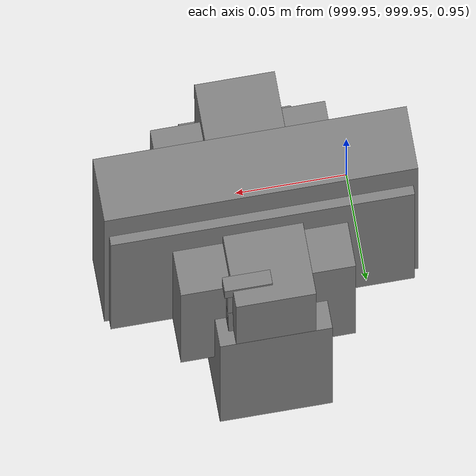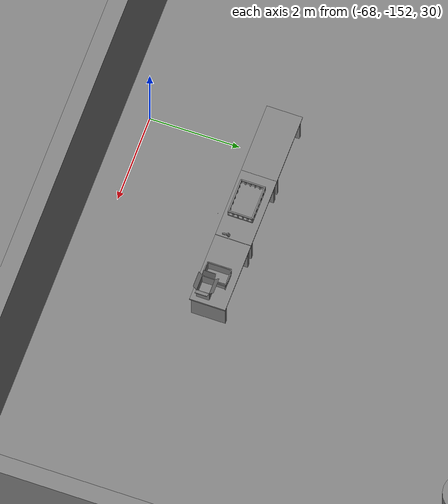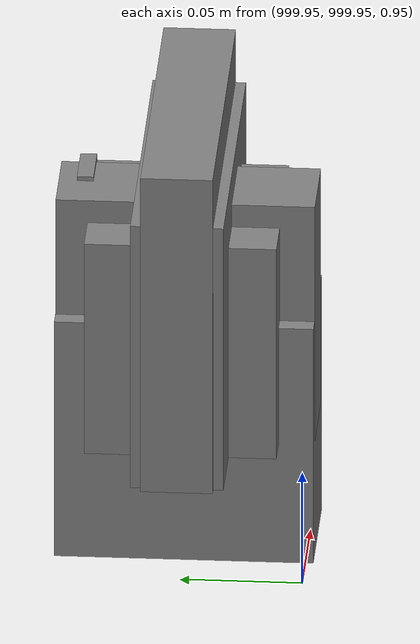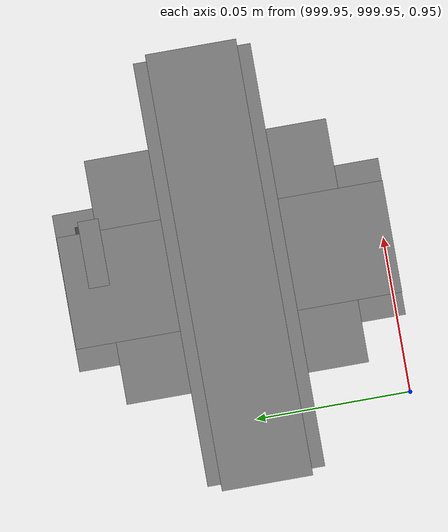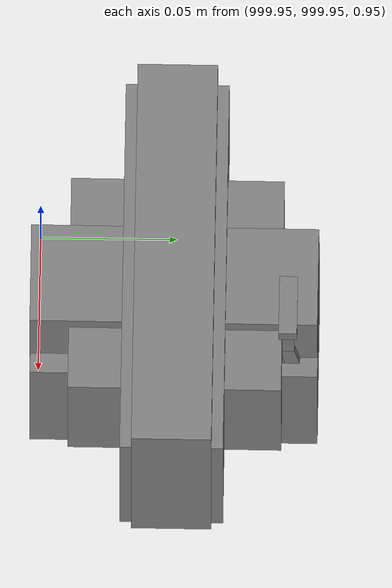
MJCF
<mujoco>
    <option gravity="0.000000000 0.000000000 -9.810000420" timestep="0.0049999999" integrator="implicitfast" density="1.225" viscosity="1.8000001e-05" noslip_iterations="10" iterations="100" sdf_iterations="50">
        <flag multiccd="disable"/>
    </option>
    <size memory="1000M"/>
    <compiler coordinate="local"/>
    <worldbody>
        <light cutoff="30" pos="0 1 1" dir="0 -1 -2"/>
        <light cutoff="30" pos="0 -1 1" dir="0 1 -2"/>
        <body pos="1000.000000000 1000.000000000 1.000000000" euler="0.000000000 0.000000000 180.000000000" name="openloong_gripper_2f85_fix_base_usda_cpu_fan">
            <geom contype="1" conaffinity="1" density="1000" type="box" material="" rgba="0.500000000 0.500000000 0.500000000 1.000000000" solimp="0.899999976 0.949999988 0.001000000" friction="1.000000000 0.005000000 0.000100000" solref="0.020000000 1.000000000" margin="0" condim="3" group="0" pos="0.000000000 0.000000000 0.070034981" quat="0.000000000 0.000000000 0.000000000 1.000000000" size="0.070700005 0.014699999 0.070700005" name="openloong_gripper_2f85_fix_base_usda_geom_B8E230D8_2795_45AF_9583_97917A89293E"/>
            <freejoint name="openloong_gripper_2f85_fix_base_usda_cpu_fan_joint"/>
            <site size="0.005000000 0.005000000 0.005000000" rgba="0.500000000 0.500000000 0.500000000 1.000000000" pos="0.000000000 0.000000000 0.000000000" quat="0.999961913 0.008726535 0.000000000 0.000000000" group="0" type="sphere" name="openloong_gripper_2f85_fix_base_usda_cpu_fancsite"/>
        </body>
        <body pos="1000.000000000 1000.000000000 1.000000000" euler="0.000000000 0.000000000 180.000000000" name="openloong_gripper_2f85_fix_base_usda_battery_01">
            <geom contype="1" conaffinity="1" density="1000" type="box" material="" rgba="0.500000000 0.500000000 0.500000000 1.000000000" solimp="0.899999976 0.949999988 0.001000000" friction="1.000000000 0.005000000 0.000100000" solref="0.020000000 1.000000000" margin="0" condim="3" group="0" pos="-0.011123657 -0.041940309 0.101691343" quat="1.000000000 0.000000000 0.000000000 0.000000000" size="0.010800000 0.003375000 0.004725000" name="openloong_gripper_2f85_fix_base_usda_geom_9C6C58EF_9415_497A_B4F7_F938FC1BE40F"/>
            <geom contype="1" conaffinity="1" density="1000" type="box" material="" rgba="0.500000000 0.500000000 0.500000000 1.000000000" solimp="0.899999976 0.949999988 0.001000000" friction="1.000000000 0.005000000 0.000100000" solref="0.020000000 1.000000000" margin="0" condim="3" group="0" pos="-0.010876465 -0.044247437 0.047066893" quat="0.998702705 -0.050920475 0.000000000 0.000000000" size="0.009450001 0.002700000 0.024975000" name="openloong_gripper_2f85_fix_base_usda_geom_ABAC319B_5CE0_4D63_A3FA_935A83350E1E"/>
            <geom contype="1" conaffinity="1" density="1000" type="box" material="" rgba="0.500000000 0.500000000 0.500000000 1.000000000" solimp="0.899999976 0.949999988 0.001000000" friction="1.000000000 0.005000000 0.000100000" solref="0.020000000 1.000000000" margin="0" condim="3" group="0" pos="-0.001235962 -0.000659180 0.047381196" quat="1.000000000 0.000000000 0.000000000 0.000000000" size="0.039420001 0.039150000 0.047250003" name="openloong_gripper_2f85_fix_base_usda_geom_79BA068D_68F9_4A09_8BB0_BA740BEBECAD"/>
            <geom contype="1" conaffinity="1" density="1000" type="box" material="" rgba="0.500000000 0.500000000 0.500000000 1.000000000" solimp="0.899999976 0.949999988 0.001000000" friction="1.000000000 0.005000000 0.000100000" solref="0.020000000 1.000000000" margin="0" condim="3" group="0" pos="-0.010876465 -0.039138794 0.009851727" quat="1.000000000 0.000000000 0.000000000 0.000000000" size="0.009450001 0.010800000 0.013500000" name="openloong_gripper_2f85_fix_base_usda_geom_AE1421EC_8B7C_40D6_BD7C_72A181028057"/>
            <geom contype="1" conaffinity="1" density="1000" type="box" material="" rgba="0.500000000 0.500000000 0.500000000 1.000000000" solimp="0.899999976 0.949999988 0.001000000" friction="1.000000000 0.005000000 0.000100000" solref="0.020000000 1.000000000" margin="0" condim="3" group="0" pos="-0.010876465 -0.041528322 0.071508206" quat="1.000000000 0.000000000 0.000000000 0.000000000" size="0.009450001 0.002700000 0.027000001" name="openloong_gripper_2f85_fix_base_usda_geom_E67969A1_990E_4F31_BA55_90A7F85AACB1"/>
            <freejoint name="openloong_gripper_2f85_fix_base_usda_battery_01_joint"/>
            <site size="0.005000000 0.005000000 0.005000000" rgba="0.500000000 0.500000000 0.500000000 1.000000000" pos="0.000000000 0.000000000 0.000000000" quat="0.999961913 0.008726500 0.000000000 0.000000000" group="0" type="sphere" name="openloong_gripper_2f85_fix_base_usda_battery_01site"/>
        </body>
        <body pos="-65.940963745 -149.312606812 31.162223816" euler="-27.967761993 80.303588867 122.049186707" mocap="true" name="spotlight4_SpotLight"/>
        <body pos="1000.000000000 1000.000000000 1.000000000" euler="0.000000000 0.000000000 180.000000000" name="openloong_gripper_2f85_fix_base_usda_wifi_box">
            <geom contype="1" conaffinity="1" density="1000" type="box" material="" rgba="0.500000000 0.500000000 0.500000000 1.000000000" solimp="0.899999976 0.949999988 0.001000000" friction="1.000000000 0.005000000 0.000100000" solref="0.020000000 1.000000000" margin="0" condim="3" group="0" pos="0.000000000 0.000000000 0.058978677" quat="0.000000000 0.000000047 0.000000000 1.000000000" size="0.068499997 0.018999999 0.059000000" name="openloong_gripper_2f85_fix_base_usda_geom_990AEBF7_4490_4478_80EF_8F2BBDF55FAE"/>
            <freejoint name="openloong_gripper_2f85_fix_base_usda_wifi_box_joint"/>
            <site size="0.005000000 0.005000000 0.005000000" rgba="0.500000000 0.500000000 0.500000000 1.000000000" pos="0.000000000 0.000000000 0.000000000" quat="0.999961913 0.008726500 0.000000000 0.000000000" group="0" type="sphere" name="openloong_gripper_2f85_fix_base_usda_wifi_boxsite"/>
        </body>
        <body pos="-66.362609863 -149.615402222 31.166366577" euler="61.398723602 33.878528595 -62.725795746" mocap="true" name="spotlight2_SpotLight"/>
        <body pos="1000.000000000 999.999938965 1.000000000" euler="0.000000000 0.000000000 180.000000000" name="openloong_gripper_2f85_fix_base_usda_intelcore_i5">
            <geom contype="1" conaffinity="1" density="1000" type="box" material="" rgba="0.500000000 0.500000000 0.500000000 1.000000000" solimp="0.899999976 0.949999988 0.001000000" friction="1.000000000 0.005000000 0.000100000" solref="0.020000000 1.000000000" margin="0" condim="3" group="0" pos="0.000000000 0.000000000 0.051722717" quat="0.707106709 0.000000000 0.000000000 -0.707106769" size="0.052800000 0.018080002 0.052800000" name="openloong_gripper_2f85_fix_base_usda_geom_56A31293_0BD6_4F48_AC79_4D362FE103F6"/>
            <freejoint name="openloong_gripper_2f85_fix_base_usda_intelcore_i5_joint"/>
            <site size="0.005000000 0.005000000 0.005000000" rgba="0.500000000 0.500000000 0.500000000 1.000000000" pos="0.000000000 0.000000000 0.000000000" quat="0.999961913 0.008726534 0.000000000 0.000000000" group="0" type="sphere" name="openloong_gripper_2f85_fix_base_usda_intelcore_i5site"/>
        </body>
        <body pos="-65.846046448 -149.446441650 31.163003922" euler="-116.683242798 -8.532605171 -165.709457397" mocap="true" name="spotlight5_SpotLight"/>
        <body pos="1000.000000000 1000.000000000 1.000000000" euler="0.000011953 0.000005123 -179.999984741" name="openloong_gripper_2f85_fix_base_usda_intel_box">
            <geom contype="1" conaffinity="1" density="1000" type="box" material="" rgba="0.500000000 0.500000000 0.500000000 1.000000000" solimp="0.899999976 0.949999988 0.001000000" friction="1.000000000 0.005000000 0.000100000" solref="0.020000000 1.000000000" margin="0" condim="3" group="0" pos="0.000000000 -0.000067139 0.000082284" quat="0.707106709 0.000000225 0.000000253 0.707106650" size="0.052800003 0.025300000 0.052800003" name="openloong_gripper_2f85_fix_base_usda_geom_943C4DDB_9130_495B_B4D0_46858C2017CE"/>
            <freejoint name="openloong_gripper_2f85_fix_base_usda_intel_box_joint"/>
            <site size="0.005000000 0.005000000 0.005000000" rgba="0.500000000 0.500000000 0.500000000 1.000000000" pos="0.000000000 0.000000000 0.000000000" quat="0.999961913 0.008726500 0.000000000 0.000000000" group="0" type="sphere" name="openloong_gripper_2f85_fix_base_usda_intel_boxsite"/>
        </body>
        <body pos="-64.866622925 -149.383972168 30.183746338" euler="89.999984741 89.999946594 0.000000000" name="openloong_gripper_2f85_fix_base_usda_bluebox_01">
            <geom contype="1" conaffinity="1" density="1000" type="box" material="" rgba="0.500000000 0.500000000 0.500000000 1.000000000" solimp="0.899999976 0.949999988 0.001000000" friction="1.000000000 0.005000000 0.000100000" solref="0.020000000 1.000000000" margin="0" condim="3" group="0" pos="0.276580811 0.187225342 0.000068665" quat="0.707106948 0.000077471 0.707106352 0.000077486" size="0.100000001 0.057999998 0.010000000" name="openloong_gripper_2f85_fix_base_usda_geom_2D655845_DB54_4B10_990C_7467836768A9"/>
            <geom contype="1" conaffinity="1" density="1000" type="box" material="" rgba="0.500000000 0.500000000 0.500000000 1.000000000" solimp="0.899999976 0.949999988 0.001000000" friction="1.000000000 0.005000000 0.000100000" solref="0.020000000 1.000000000" margin="0" condim="3" group="0" pos="0.000000000 0.002883911 0.000000000" quat="0.999999881 0.000000000 0.000000000 0.000000000" size="0.254000008 0.003000000 0.172000006" name="openloong_gripper_2f85_fix_base_usda_geom_905AE1B2_8BC1_4446_BA3D_6C2262604A96"/>
            <geom contype="1" conaffinity="1" density="1000" type="box" material="" rgba="0.500000000 0.500000000 0.500000000 1.000000000" solimp="0.899999976 0.949999988 0.001000000" friction="1.000000000 0.005000000 0.000100000" solref="0.020000000 1.000000000" margin="0" condim="3" group="0" pos="0.000000000 0.124874115 0.173484802" quat="0.999796331 0.020176515 -0.000000015 0.000000030" size="0.259999990 0.119999997 0.007000000" name="openloong_gripper_2f85_fix_base_usda_geom_D8633682_BCCD_4F9A_AC6D_51787E61D4E3"/>
            <geom contype="1" conaffinity="1" density="1000" type="box" material="" rgba="0.500000000 0.500000000 0.500000000 1.000000000" solimp="0.899999976 0.949999988 0.001000000" friction="1.000000000 0.005000000 0.000100000" solref="0.020000000 1.000000000" margin="0" condim="3" group="0" pos="0.000000000 0.124874115 -0.173469543" quat="0.999796331 -0.020176545 -0.000000015 0.000000000" size="0.259999990 0.119999997 0.007000000" name="openloong_gripper_2f85_fix_base_usda_geom_5FEAD07E_B2D5_42A7_A5B5_CE96EFCC9138"/>
            <geom contype="1" conaffinity="1" density="1000" type="box" material="" rgba="0.500000000 0.500000000 0.500000000 1.000000000" solimp="0.899999976 0.949999988 0.001000000" friction="1.000000000 0.005000000 0.000100000" solref="0.020000000 1.000000000" margin="0" condim="3" group="0" pos="0.000000000 0.214008331 0.188980103" quat="0.999912977 0.013176724 0.000000015 0.000000000" size="0.259999990 0.029999999 0.012500000" name="openloong_gripper_2f85_fix_base_usda_geom_2D3615F4_7170_4043_8588_40BC1CB09E51"/>
            <geom contype="1" conaffinity="1" density="1000" type="box" material="" rgba="0.500000000 0.500000000 0.500000000 1.000000000" solimp="0.899999976 0.949999988 0.001000000" friction="1.000000000 0.005000000 0.000100000" solref="0.020000000 1.000000000" margin="0" condim="3" group="0" pos="-0.258361816 0.125289917 0.001876831" quat="0.702796936 -0.020792112 0.710783124 0.020769298" size="0.189999998 0.119999997 0.009000000" name="openloong_gripper_2f85_fix_base_usda_geom_E855E0D1_D5ED_4A9B_85E7_31F4FF3F2B24"/>
            <geom contype="1" conaffinity="1" density="1000" type="box" material="" rgba="0.500000000 0.500000000 0.500000000 1.000000000" solimp="0.899999976 0.949999988 0.001000000" friction="1.000000000 0.005000000 0.000100000" solref="0.020000000 1.000000000" margin="0" condim="3" group="0" pos="0.000000000 0.214008331 -0.188980103" quat="0.999912977 -0.013176769 0.000000030 0.000000015" size="0.259999990 0.029999999 0.012500000" name="openloong_gripper_2f85_fix_base_usda_geom_9C7D0D51_E9B1_4EF4_9849_0A6E0E14B75F"/>
            <geom contype="1" conaffinity="1" density="1000" type="box" material="" rgba="0.500000000 0.500000000 0.500000000 1.000000000" solimp="0.899999976 0.949999988 0.001000000" friction="1.000000000 0.005000000 0.000100000" solref="0.020000000 1.000000000" margin="0" condim="3" group="0" pos="-0.276611328 0.187225342 0.000068665" quat="0.707106650 0.000077441 0.707106709 0.000077456" size="0.100000001 0.057999998 0.010000000" name="openloong_gripper_2f85_fix_base_usda_geom_6FD9F497_3E2F_4720_941A_DC04CDD8A0D3"/>
            <geom contype="1" conaffinity="1" density="1000" type="box" material="" rgba="0.500000000 0.500000000 0.500000000 1.000000000" solimp="0.899999976 0.949999988 0.001000000" friction="1.000000000 0.005000000 0.000100000" solref="0.020000000 1.000000000" margin="0" condim="3" group="0" pos="0.258331299 0.125289917 0.001876831" quat="0.702851415 0.018856421 0.710823774 -0.019329369" size="0.189999998 0.119999997 0.009000000" name="openloong_gripper_2f85_fix_base_usda_geom_B4D68638_6D2D_435C_90FC_A1B503E11ED3"/>
            <freejoint name="openloong_gripper_2f85_fix_base_usda_bluebox_01_joint"/>
            <site size="0.005000000 0.005000000 0.005000000" rgba="0.500000000 0.500000000 0.500000000 1.000000000" pos="0.000000000 0.000000000 0.000000000" quat="0.999961913 0.008726534 0.000000000 0.000000000" group="0" type="sphere" name="openloong_gripper_2f85_fix_base_usda_bluebox_01site"/>
        </body>
        <body pos="-64.496299744 -149.491867065 30.235729218" euler="0.000000000 0.000000000 89.999946594" name="openloong_gripper_2f85_fix_base_usda_cardboardbox_01">
            <geom contype="1" conaffinity="1" density="1000" type="box" material="" rgba="0.500000000 0.500000000 0.500000000 1.000000000" solimp="0.899999976 0.949999988 0.001000000" friction="1.000000000 0.005000000 0.000100000" solref="0.020000000 1.000000000" margin="0" condim="3" group="0" pos="-0.003166199 -0.004086494 0.005052090" quat="1.000000000 0.000000000 0.000000000 0.000000000" size="0.142499998 0.177500010 0.005000000" name="openloong_gripper_2f85_fix_base_usda_geom_8E91983F_1F14_4F23_AEB4_CED5256D6F2C"/>
            <geom contype="1" conaffinity="1" density="1000" type="box" material="" rgba="0.500000000 0.500000000 0.500000000 1.000000000" solimp="0.899999976 0.949999988 0.001000000" friction="1.000000000 0.005000000 0.000100000" solref="0.020000000 1.000000000" margin="0" condim="3" group="0" pos="-0.003166199 0.170316696 0.150570869" quat="1.000000000 0.000000000 0.000000000 0.000000000" size="0.142499998 0.005000000 0.149999991" name="openloong_gripper_2f85_fix_base_usda_geom_1B49C3E7_FEB5_4ED6_9236_7F69AD7190CF"/>
            <geom contype="1" conaffinity="1" density="1000" type="box" material="" rgba="0.500000000 0.500000000 0.500000000 1.000000000" solimp="0.899999976 0.949999988 0.001000000" friction="1.000000000 0.005000000 0.000100000" solref="0.020000000 1.000000000" margin="0" condim="3" group="0" pos="-0.147399902 -0.005307198 0.150570869" quat="1.000000000 0.000000000 0.000000000 0.000000000" size="0.005000000 0.177500010 0.149999991" name="openloong_gripper_2f85_fix_base_usda_geom_7DE2831A_888F_4354_AD90_AF8FF888F2F4"/>
            <geom contype="1" conaffinity="1" density="1000" type="box" material="" rgba="0.500000000 0.500000000 0.500000000 1.000000000" solimp="0.899999976 0.949999988 0.001000000" friction="1.000000000 0.005000000 0.000100000" solref="0.020000000 1.000000000" margin="0" condim="3" group="0" pos="0.140275955 -0.005307198 0.150570869" quat="1.000000000 0.000000000 0.000000000 0.000000000" size="0.005000000 0.177500010 0.149999991" name="openloong_gripper_2f85_fix_base_usda_geom_AAB28D1A_1D9F_4A4A_A87B_C8F424CEDE90"/>
            <geom contype="1" conaffinity="1" density="1000" type="box" material="" rgba="0.500000000 0.500000000 0.500000000 1.000000000" solimp="0.899999976 0.949999988 0.001000000" friction="1.000000000 0.005000000 0.000100000" solref="0.020000000 1.000000000" margin="0" condim="3" group="0" pos="-0.003166199 -0.181550980 0.150570869" quat="1.000000000 0.000000000 0.000000000 0.000000000" size="0.142499998 0.005000000 0.149999991" name="openloong_gripper_2f85_fix_base_usda_geom_C8A91097_2913_48D2_A033_250FFCFE255F"/>
            <freejoint name="openloong_gripper_2f85_fix_base_usda_cardboardbox_01_joint"/>
            <site size="0.005000000 0.005000000 0.005000000" rgba="0.500000000 0.500000000 0.500000000 1.000000000" pos="0.000000000 0.000000000 0.000000000" quat="0.999961913 0.008726535 0.000000000 0.000000000" group="0" type="sphere" name="openloong_gripper_2f85_fix_base_usda_site_4B41CF36_7F25_4A56_BCCF_1644E5F5449F"/>
            <body pos="0.139160156 -0.004048347 0.301930904" euler="-179.999954224 49.383502960 179.999954224" name="openloong_gripper_2f85_fix_base_usda_A1_006">
                <geom contype="1" conaffinity="1" density="1000" type="box" material="" rgba="0.500000000 0.500000000 0.500000000 1.000000000" solimp="0.899999976 0.949999988 0.001000000" friction="1.000000000 0.005000000 0.000100000" solref="0.020000000 1.000000000" margin="0" condim="3" group="0" pos="-0.071587563 0.000009537 0.001745224" quat="0.999999881 0.000000000 0.000000000 0.000000000" size="0.071249999 0.179999992 0.002500000" name="openloong_gripper_2f85_fix_base_usda_geom_D3AC5657_18DA_42AE_AA8F_A0FA74584D12"/>
                <joint armature="0" stiffness="0.07" damping="0.0099999998" axis="0.000000 1.000000 0.000000" type="hinge" name="openloong_gripper_2f85_fix_base_usda_A1_006"/>
            </body>
            <body pos="-0.145902634 -0.004086494 0.301938057" euler="-180.000000000 -60.000011444 -180.000000000" name="openloong_gripper_2f85_fix_base_usda_A2_006">
                <geom contype="1" conaffinity="1" density="1000" type="box" material="" rgba="0.500000000 0.500000000 0.500000000 1.000000000" solimp="0.899999976 0.949999988 0.001000000" friction="1.000000000 0.005000000 0.000100000" solref="0.020000000 1.000000000" margin="0" condim="3" group="0" pos="0.071268082 0.000009537 0.002717972" quat="0.000002921 0.000000000 -0.000000030 0.999999881" size="0.071249999 0.179999992 0.002500000" name="openloong_gripper_2f85_fix_base_usda_geom_596FDDBA_D45F_40B2_AB88_DF4FB5DDE209"/>
                <joint armature="0" stiffness="0.07" damping="0.0099999998" axis="0.000000 1.000000 0.000000" type="hinge" name="openloong_gripper_2f85_fix_base_usda_A2_006"/>
            </body>
            <body pos="-0.003385544 0.175991058 0.301930904" euler="-125.858116150 -0.000004561 0.000002331" name="openloong_gripper_2f85_fix_base_usda_B2_006">
                <geom contype="1" conaffinity="1" density="1000" type="box" material="" rgba="0.500000000 0.500000000 0.500000000 1.000000000" solimp="0.899999976 0.949999988 0.001000000" friction="1.000000000 0.005000000 0.000100000" solref="0.020000000 1.000000000" margin="0" condim="3" group="0" pos="0.000009537 -0.070939064 -0.002470016" quat="0.999614120 0.027776197 -0.000000015 0.000000030" size="0.137500003 0.064999998 0.005000000" name="openloong_gripper_2f85_fix_base_usda_geom_860C4187_A4D5_4930_AAF6_57D19F20BC73"/>
                <joint armature="0" stiffness="0.07" damping="0.0099999998" axis="1.000000 0.000000 0.000000" type="hinge" name="openloong_gripper_2f85_fix_base_usda_B2_006"/>
            </body>
            <body pos="-0.003385544 -0.184140205 0.301938057" euler="147.805557251 0.000000000 0.000000000" name="openloong_gripper_2f85_fix_base_usda_B1_006">
                <geom contype="1" conaffinity="1" density="1000" type="box" material="" rgba="0.500000000 0.500000000 0.500000000 1.000000000" solimp="0.899999976 0.949999988 0.001000000" friction="1.000000000 0.005000000 0.000100000" solref="0.020000000 1.000000000" margin="0" condim="3" group="0" pos="-0.000028610 0.070202351 -0.002703667" quat="0.999614179 -0.027776167 0.000000000 0.000000000" size="0.137500003 0.064999998 0.005000000" name="openloong_gripper_2f85_fix_base_usda_geom_97306CE2_B460_4593_AC51_ACA95C9C7F94"/>
                <joint armature="0" stiffness="0.07" damping="0.0099999998" axis="1.000000 0.000000 0.000000" type="hinge" name="openloong_gripper_2f85_fix_base_usda_B1_006"/>
            </body>
        </body>
        <body pos="-65.882858276 -149.481979370 30.229999542" euler="-64.487716675 0.000000000 0.000000000" name="openloong_gripper_2f85_fix_base_usda_Barcode">
            <geom contype="1" conaffinity="1" density="1000" type="box" material="" rgba="0.500000000 0.500000000 0.500000000 1.000000000" solimp="0.899999976 0.949999988 0.001000000" friction="1.000000000 0.005000000 0.000100000" solref="0.020000000 1.000000000" margin="0" condim="3" group="0" pos="0.000000000 0.013038635 0.001419067" quat="0.000000000 0.000000000 0.000000000 1.000000119" size="0.034000002 0.010000000 0.017999999" name="openloong_gripper_2f85_fix_base_usda_geom_6F3ED04E_B2A2_44A3_850B_3E248702EB5E"/>
            <geom contype="1" conaffinity="1" density="1000" type="box" material="" rgba="0.500000000 0.500000000 0.500000000 1.000000000" solimp="0.899999976 0.949999988 0.001000000" friction="1.000000000 0.005000000 0.000100000" solref="0.020000000 1.000000000" margin="0" condim="3" group="0" pos="0.000000000 -0.035301208 -0.007095337" quat="0.000000000 0.000000000 -0.043619365 0.999048233" size="0.028999999 0.010000000 0.020000000" name="openloong_gripper_2f85_fix_base_usda_geom_324D3A95_0F7B_4301_8D9B_93572B098F9E"/>
            <geom contype="1" conaffinity="1" density="1000" type="box" material="" rgba="0.500000000 0.500000000 0.500000000 1.000000000" solimp="0.899999976 0.949999988 0.001000000" friction="1.000000000 0.005000000 0.000100000" solref="0.020000000 1.000000000" margin="0" condim="3" group="0" pos="0.000000000 -0.043411255 -0.011749268" quat="0.922262907 0.386563420 0.000000000 0.000000000" size="0.026000001 0.010000000 0.020000000" name="openloong_gripper_2f85_fix_base_usda_geom_E44EB752_8CF0_4356_BC38_F55713198A90"/>
            <geom contype="1" conaffinity="1" density="1000" type="box" material="" rgba="0.500000000 0.500000000 0.500000000 1.000000000" solimp="0.899999976 0.949999988 0.001000000" friction="1.000000000 0.005000000 0.000100000" solref="0.020000000 1.000000000" margin="0" condim="3" group="0" pos="0.000000000 -0.016967773 -0.031860352" quat="0.000000000 0.000000000 0.000000000 1.000000119" size="0.008000000 0.010000000 0.013000000" name="openloong_gripper_2f85_fix_base_usda_geom_78243D7E_EF43_43F0_98F8_B35BA7D42A73"/>
            <geom contype="1" conaffinity="1" density="1000" type="box" material="" rgba="0.500000000 0.500000000 0.500000000 1.000000000" solimp="0.899999976 0.949999988 0.001000000" friction="1.000000000 0.005000000 0.000100000" solref="0.020000000 1.000000000" margin="0" condim="3" group="0" pos="0.000000000 -0.001869202 0.000312805" quat="0.953716993 0.300705761 0.000000000 0.000000000" size="0.032000002 0.010000000 0.018999999" name="openloong_gripper_2f85_fix_base_usda_geom_23E138E3_EC3B_4B84_867D_825F13FA182D"/>
            <geom contype="1" conaffinity="1" density="1000" type="box" material="" rgba="0.500000000 0.500000000 0.500000000 1.000000000" solimp="0.899999976 0.949999988 0.001000000" friction="1.000000000 0.005000000 0.000100000" solref="0.020000000 1.000000000" margin="0" condim="3" group="0" pos="0.000000000 -0.019531250 -0.003173828" quat="0.953716993 0.300705761 0.000000000 0.000000000" size="0.030999999 0.010000000 0.020000000" name="openloong_gripper_2f85_fix_base_usda_geom_ACA53B85_BFB9_48F5_9C8D_11B9E9FEB847"/>
            <geom contype="1" conaffinity="1" density="1000" type="box" material="" rgba="0.500000000 0.500000000 0.500000000 1.000000000" solimp="0.899999976 0.949999988 0.001000000" friction="1.000000000 0.005000000 0.000100000" solref="0.020000000 1.000000000" margin="0" condim="3" group="0" pos="0.000000000 -0.035301208 -0.007095337" quat="0.953716993 0.300705761 0.000000000 0.000000000" size="0.028999999 0.010000000 0.020000000" name="openloong_gripper_2f85_fix_base_usda_geom_5631C5A5_8B26_4234_8FBB_526D3B89F825"/>
            <geom contype="1" conaffinity="1" density="1000" type="box" material="" rgba="0.500000000 0.500000000 0.500000000 1.000000000" solimp="0.899999976 0.949999988 0.001000000" friction="1.000000000 0.005000000 0.000100000" solref="0.020000000 1.000000000" margin="0" condim="3" group="0" pos="0.000000000 -0.042617798 -0.071121216" quat="0.000000000 0.000000000 0.000000000 1.000000119" size="0.013000000 0.021000000 0.059999999" name="openloong_gripper_2f85_fix_base_usda_geom_CD0C9566_1DAD_4908_9D66_CD33D8BC18E8"/>
            <freejoint name="openloong_gripper_2f85_fix_base_usda_Barcode_joint"/>
            <site size="0.005000000 0.005000000 0.005000000" rgba="0.500000000 0.500000000 0.500000000 1.000000000" pos="0.000000000 0.000000000 0.000000000" quat="1.000000000 0.000000000 0.000000000 0.000000000" group="0" type="sphere" name="openloong_gripper_2f85_fix_base_usda_Barcode_site"/>
        </body>
        <body pos="-66.745018005 -149.392349243 30.184000015" euler="0.000000000 0.000000000 89.999946594" name="[22332640507998]_Basket_01">
            <geom contype="1" conaffinity="1" density="1000" type="box" material="" rgba="0.500000000 0.500000000 0.500000000 1.000000000" solimp="0.899999976 0.949999988 0.001000000" friction="1.000000000 0.005000000 0.000100000" solref="0.020000000 1.000000000" margin="0" condim="3" group="0" pos="-0.052425385 0.389207840 0.089787483" quat="0.707107008 0.000000000 0.000000000 0.707106411" size="0.014249999 0.014249999 0.059999999" name="[22332640507998]_geom_8CA56C72_CDE5_41C9_8130_BA68950A0E5F"/>
            <geom contype="1" conaffinity="1" density="1000" type="box" material="" rgba="0.500000000 0.500000000 0.500000000 1.000000000" solimp="0.899999976 0.949999988 0.001000000" friction="1.000000000 0.005000000 0.000100000" solref="0.020000000 1.000000000" margin="0" condim="3" group="0" pos="0.264015198 -0.133043289 0.089787483" quat="0.707107008 0.000000000 0.000000000 0.707106411" size="0.014249999 0.014249999 0.059999999" name="[22332640507998]_geom_42321D05_45C1_41CE_BED3_29C46C7CD2A4"/>
            <geom contype="1" conaffinity="1" density="1000" type="box" material="" rgba="0.500000000 0.500000000 0.500000000 1.000000000" solimp="0.899999976 0.949999988 0.001000000" friction="1.000000000 0.005000000 0.000100000" solref="0.020000000 1.000000000" margin="0" condim="3" group="0" pos="-0.264015198 -0.265548706 0.089793205" quat="0.707107008 0.000000000 0.000000000 0.707106411" size="0.014249999 0.014249999 0.059999999" name="[22332640507998]_geom_550697A5_6EF3_4F80_A046_522C8720C1FE"/>
            <geom contype="1" conaffinity="1" density="1000" type="box" material="" rgba="0.500000000 0.500000000 0.500000000 1.000000000" solimp="0.899999976 0.949999988 0.001000000" friction="1.000000000 0.005000000 0.000100000" solref="0.020000000 1.000000000" margin="0" condim="3" group="0" pos="-0.160263062 -0.389322281 0.089793205" quat="0.707107008 0.000000000 0.000000000 0.707106411" size="0.014249999 0.014249999 0.059999999" name="[22332640507998]_geom_F3944413_2501_4A1B_9463_9FD0B502C8AB"/>
            <geom contype="1" conaffinity="1" density="1000" type="box" material="" rgba="0.500000000 0.500000000 0.500000000 1.000000000" solimp="0.899999976 0.949999988 0.001000000" friction="1.000000000 0.005000000 0.000100000" solref="0.020000000 1.000000000" margin="0" condim="3" group="0" pos="0.162265778 -0.389322281 0.089787483" quat="0.707107008 0.000000000 0.000000000 0.707106411" size="0.014249999 0.014249999 0.059999999" name="[22332640507998]_geom_1E08191B_DD0E_44F9_9B2B_795D5B1CCBCB"/>
            <geom contype="1" conaffinity="1" density="1000" type="box" material="" rgba="0.500000000 0.500000000 0.500000000 1.000000000" solimp="0.899999976 0.949999988 0.001000000" friction="1.000000000 0.005000000 0.000100000" solref="0.020000000 1.000000000" margin="0" condim="3" group="0" pos="0.264015198 0.389207840 0.089787483" quat="0.707107008 0.000000000 0.000000000 0.707106411" size="0.014249999 0.014249999 0.059999999" name="[22332640507998]_geom_E3BA0F4B_4154_4164_BBF3_49B033C80DD0"/>
            <geom contype="1" conaffinity="1" density="1000" type="box" material="" rgba="0.500000000 0.500000000 0.500000000 1.000000000" solimp="0.899999976 0.949999988 0.001000000" friction="1.000000000 0.005000000 0.000100000" solref="0.020000000 1.000000000" margin="0" condim="3" group="0" pos="-0.264015198 -0.133043289 0.089793205" quat="0.707107008 0.000000000 0.000000000 0.707106411" size="0.014249999 0.014249999 0.059999999" name="[22332640507998]_geom_FE17EAB6_DD89_4135_A483_8D0F867F5AE7"/>
            <geom contype="1" conaffinity="1" density="1000" type="box" material="" rgba="0.500000000 0.500000000 0.500000000 1.000000000" solimp="0.899999976 0.949999988 0.001000000" friction="1.000000000 0.005000000 0.000100000" solref="0.020000000 1.000000000" margin="0" condim="3" group="0" pos="-0.264026642 0.269256592 0.089793205" quat="0.707107008 0.000000000 0.000000000 0.707106411" size="0.014249999 0.014249999 0.059999999" name="[22332640507998]_geom_34C67EC1_7CF3_4907_B875_AE66A19FC119"/>
            <geom contype="1" conaffinity="1" density="1000" type="box" material="" rgba="0.500000000 0.500000000 0.500000000 1.000000000" solimp="0.899999976 0.949999988 0.001000000" friction="1.000000000 0.005000000 0.000100000" solref="0.020000000 1.000000000" margin="0" condim="3" group="0" pos="0.054462433 0.389207840 0.089787483" quat="0.707107008 0.000000000 0.000000000 0.707106411" size="0.014249999 0.014249999 0.059999999" name="[22332640507998]_geom_1FA7C87D_4719_4D60_A151_5C8842D65DD4"/>
            <geom contype="1" conaffinity="1" density="1000" type="box" material="" rgba="0.500000000 0.500000000 0.500000000 1.000000000" solimp="0.899999976 0.949999988 0.001000000" friction="1.000000000 0.005000000 0.000100000" solref="0.020000000 1.000000000" margin="0" condim="3" group="0" pos="0.054462433 -0.389322281 0.089787483" quat="0.707107008 0.000000000 0.000000000 0.707106411" size="0.014249999 0.014249999 0.059999999" name="[22332640507998]_geom_80309DEA_B213_4132_BBA6_7C41F532E078"/>
            <geom contype="1" conaffinity="1" density="1000" type="box" material="" rgba="0.500000000 0.500000000 0.500000000 1.000000000" solimp="0.899999976 0.949999988 0.001000000" friction="1.000000000 0.005000000 0.000100000" solref="0.020000000 1.000000000" margin="0" condim="3" group="0" pos="0.264015198 0.269256592 0.089793205" quat="0.707107008 0.000000000 0.000000000 0.707106411" size="0.014249999 0.014249999 0.059999999" name="[22332640507998]_geom_9D6B2771_58E0_4731_BF02_82113496C66B"/>
            <geom contype="1" conaffinity="1" density="1000" type="box" material="" rgba="0.500000000 0.500000000 0.500000000 1.000000000" solimp="0.899999976 0.949999988 0.001000000" friction="1.000000000 0.005000000 0.000100000" solref="0.020000000 1.000000000" margin="0" condim="3" group="0" pos="0.264015198 -0.389322281 0.089787483" quat="0.707107008 0.000000000 0.000000000 0.707106411" size="0.014249999 0.014249999 0.059999999" name="[22332640507998]_geom_2FD23C71_0CF6_42BF_A13E_C7F69673E88D"/>
            <geom contype="1" conaffinity="1" density="1000" type="box" material="" rgba="0.500000000 0.500000000 0.500000000 1.000000000" solimp="0.899999976 0.949999988 0.001000000" friction="1.000000000 0.005000000 0.000100000" solref="0.020000000 1.000000000" margin="0" condim="3" group="0" pos="0.000000000 0.000000000 0.015998840" quat="0.707107008 0.000000000 0.000000000 0.707106411" size="0.403499991 0.279000014 0.015750000" name="[22332640507998]_geom_7631557A_CD6A_4E38_84E4_1739048EB8AC"/>
            <geom contype="1" conaffinity="1" density="1000" type="box" material="" rgba="0.500000000 0.500000000 0.500000000 1.000000000" solimp="0.899999976 0.949999988 0.001000000" friction="1.000000000 0.005000000 0.000100000" solref="0.020000000 1.000000000" margin="0" condim="3" group="0" pos="0.000000000 -0.389476776 0.163619041" quat="0.707107008 0.000000000 0.000000000 0.707106411" size="0.015000000 0.277500004 0.015750000" name="[22332640507998]_geom_C6458779_BD63_4955_951C_52AA671A0A00"/>
            <geom contype="1" conaffinity="1" density="1000" type="box" material="" rgba="0.500000000 0.500000000 0.500000000 1.000000000" solimp="0.899999976 0.949999988 0.001000000" friction="1.000000000 0.005000000 0.000100000" solref="0.020000000 1.000000000" margin="0" condim="3" group="0" pos="0.162265778 0.389207840 0.089787483" quat="0.707107008 0.000000000 0.000000000 0.707106411" size="0.014249999 0.014249999 0.059999999" name="[22332640507998]_geom_C0E67205_5F60_4AD2_ACE2_2AAEC72D5986"/>
            <geom contype="1" conaffinity="1" density="1000" type="box" material="" rgba="0.500000000 0.500000000 0.500000000 1.000000000" solimp="0.899999976 0.949999988 0.001000000" friction="1.000000000 0.005000000 0.000100000" solref="0.020000000 1.000000000" margin="0" condim="3" group="0" pos="0.000000000 0.389471054 0.163619041" quat="0.707107008 0.000000000 0.000000000 0.707106411" size="0.015000000 0.277500004 0.015750000" name="[22332640507998]_geom_FA1F52C4_E10A_4745_91F5_90BA3C1C43A6"/>
            <geom contype="1" conaffinity="1" density="1000" type="box" material="" rgba="0.500000000 0.500000000 0.500000000 1.000000000" solimp="0.899999976 0.949999988 0.001000000" friction="1.000000000 0.005000000 0.000100000" solref="0.020000000 1.000000000" margin="0" condim="3" group="0" pos="-0.263511658 0.000000000 0.163619041" quat="0.707107008 0.000000000 0.000000000 0.707106411" size="0.403499991 0.015000000 0.015750000" name="[22332640507998]_geom_6BC8A6C8_E689_4F0D_BAA1_03FC86A40EFA"/>
            <geom contype="1" conaffinity="1" density="1000" type="box" material="" rgba="0.500000000 0.500000000 0.500000000 1.000000000" solimp="0.899999976 0.949999988 0.001000000" friction="1.000000000 0.005000000 0.000100000" solref="0.020000000 1.000000000" margin="0" condim="3" group="0" pos="-0.264015198 0.141334534 0.089793205" quat="0.707107008 0.000000000 0.000000000 0.707106411" size="0.014249999 0.014249999 0.059999999" name="[22332640507998]_geom_AD2C94DD_1D0D_47B9_9C74_7AB2E3F63A19"/>
            <geom contype="1" conaffinity="1" density="1000" type="box" material="" rgba="0.500000000 0.500000000 0.500000000 1.000000000" solimp="0.899999976 0.949999988 0.001000000" friction="1.000000000 0.005000000 0.000100000" solref="0.020000000 1.000000000" margin="0" condim="3" group="0" pos="0.264015198 -0.265548706 0.089787483" quat="0.707107008 0.000000000 0.000000000 0.707106411" size="0.014249999 0.014249999 0.059999999" name="[22332640507998]_geom_14DD06FF_0D00_4B43_A74E_ED5A1D49FAA8"/>
            <geom contype="1" conaffinity="1" density="1000" type="box" material="" rgba="0.500000000 0.500000000 0.500000000 1.000000000" solimp="0.899999976 0.949999988 0.001000000" friction="1.000000000 0.005000000 0.000100000" solref="0.020000000 1.000000000" margin="0" condim="3" group="0" pos="-0.160263062 0.389207840 0.089787483" quat="0.707107008 0.000000000 0.000000000 0.707106411" size="0.014249999 0.014249999 0.059999999" name="[22332640507998]_geom_F43D6D43_D26C_4C0A_8038_8D79FEC167EC"/>
            <geom contype="1" conaffinity="1" density="1000" type="box" material="" rgba="0.500000000 0.500000000 0.500000000 1.000000000" solimp="0.899999976 0.949999988 0.001000000" friction="1.000000000 0.005000000 0.000100000" solref="0.020000000 1.000000000" margin="0" condim="3" group="0" pos="-0.052425385 -0.389322281 0.089787483" quat="0.707107008 0.000000000 0.000000000 0.707106411" size="0.014249999 0.014249999 0.059999999" name="[22332640507998]_geom_8D7386CF_1C45_496C_BB5F_A738614A4B48"/>
            <geom contype="1" conaffinity="1" density="1000" type="box" material="" rgba="0.500000000 0.500000000 0.500000000 1.000000000" solimp="0.899999976 0.949999988 0.001000000" friction="1.000000000 0.005000000 0.000100000" solref="0.020000000 1.000000000" margin="0" condim="3" group="0" pos="-0.264026642 -0.389322281 0.089793205" quat="0.707107008 0.000000000 0.000000000 0.707106411" size="0.014249999 0.014249999 0.059999999" name="[22332640507998]_geom_A6E99BFE_5E60_402B_966F_CE4B8E659E44"/>
            <geom contype="1" conaffinity="1" density="1000" type="box" material="" rgba="0.500000000 0.500000000 0.500000000 1.000000000" solimp="0.899999976 0.949999988 0.001000000" friction="1.000000000 0.005000000 0.000100000" solref="0.020000000 1.000000000" margin="0" condim="3" group="0" pos="0.264015198 0.141334534 0.089787483" quat="0.707107008 0.000000000 0.000000000 0.707106411" size="0.014249999 0.014249999 0.059999999" name="[22332640507998]_geom_8822E56D_2935_46EA_AF32_B69B87A12289"/>
            <geom contype="1" conaffinity="1" density="1000" type="box" material="" rgba="0.500000000 0.500000000 0.500000000 1.000000000" solimp="0.899999976 0.949999988 0.001000000" friction="1.000000000 0.005000000 0.000100000" solref="0.020000000 1.000000000" margin="0" condim="3" group="0" pos="-0.264015198 0.389207840 0.089793205" quat="0.707107008 0.000000000 0.000000000 0.707106411" size="0.014249999 0.014249999 0.059999999" name="[22332640507998]_geom_79F0CA18_AD39_43D4_B5E7_06DBC6720218"/>
            <geom contype="1" conaffinity="1" density="1000" type="box" material="" rgba="0.500000000 0.500000000 0.500000000 1.000000000" solimp="0.899999976 0.949999988 0.001000000" friction="1.000000000 0.005000000 0.000100000" solref="0.020000000 1.000000000" margin="0" condim="3" group="0" pos="0.264015198 0.004480362 0.089787483" quat="0.707107008 0.000000000 0.000000000 0.707106411" size="0.014249999 0.014249999 0.059999999" name="[22332640507998]_geom_961AC012_CAFF_493E_BE6A_2E9775468266"/>
            <geom contype="1" conaffinity="1" density="1000" type="box" material="" rgba="0.500000000 0.500000000 0.500000000 1.000000000" solimp="0.899999976 0.949999988 0.001000000" friction="1.000000000 0.005000000 0.000100000" solref="0.020000000 1.000000000" margin="0" condim="3" group="0" pos="0.263694763 -0.000011444 0.163619041" quat="0.707107008 0.000000000 0.000000000 0.707106411" size="0.403499991 0.015000000 0.015750000" name="[22332640507998]_geom_7A170D15_1686_4EEA_83E9_0529DB3000DA"/>
            <geom contype="1" conaffinity="1" density="1000" type="box" material="" rgba="0.500000000 0.500000000 0.500000000 1.000000000" solimp="0.899999976 0.949999988 0.001000000" friction="1.000000000 0.005000000 0.000100000" solref="0.020000000 1.000000000" margin="0" condim="3" group="0" pos="-0.264015198 0.004480362 0.089793205" quat="0.707107008 0.000000000 0.000000000 0.707106411" size="0.014249999 0.014249999 0.059999999" name="[22332640507998]_geom_5DC18512_C46F_41C1_8731_BA221FF2090D"/>
            <freejoint name="[22332640507998]_joint_F673EDD2_120A_4A61_AA11_4C842F46F5C1"/>
        </body>
        <body pos="0.000000000 0.000000000 0.000000000" euler="0.000000000 0.000000000 0.000000000" name="Static Objects_Static Objects">
            <geom contype="1" conaffinity="1" density="1000" type="box" material="" rgba="0.500000000 0.500000000 0.500000000 1.000000000" solimp="0.899999976 0.949999988 0.001000000" friction="1.000000000 0.005000000 0.000100000" solref="0.020000000 1.000000000" margin="0" condim="3" group="0" pos="-67.544113159 -149.365814209 29.727830887" quat="0.500000417 0.499999970 0.499999553 0.499999970" size="0.381000012 0.319999993 0.041000001" name="Static Objects_geom_CA83A846_B7A7_4B14_A909_3F09E620FA71"/>
            <geom contype="1" conaffinity="1" density="1000" type="box" material="" rgba="0.500000000 0.500000000 0.500000000 1.000000000" solimp="0.899999976 0.949999988 0.001000000" friction="1.000000000 0.005000000 0.000100000" solref="0.020000000 1.000000000" margin="0" condim="3" group="0" pos="-68.239501953 -149.365814209 30.086868286" quat="0.500000417 0.499999970 0.499999553 0.499999970" size="0.370999992 0.039500002 0.745000005" name="Static Objects_geom_6D34EB62_E3AA_4228_9465_CEB79227659A"/>
            <geom contype="1" conaffinity="1" density="1000" type="box" material="" rgba="0.500000000 0.500000000 0.500000000 1.000000000" solimp="0.899999976 0.949999988 0.001000000" friction="1.000000000 0.005000000 0.000100000" solref="0.020000000 1.000000000" margin="0" condim="3" group="0" pos="-68.239501953 -149.365814209 30.147235870" quat="0.500000417 0.499999970 0.499999553 0.499999970" size="0.400000006 0.022000000 0.800000012" name="Static Objects_geom_BF0666CD_9C9A_44BC_B65D_5B4986F0FD86"/>
            <geom contype="1" conaffinity="1" density="1000" type="box" material="" rgba="0.500000000 0.500000000 0.500000000 1.000000000" solimp="0.899999976 0.949999988 0.001000000" friction="1.000000000 0.005000000 0.000100000" solref="0.020000000 1.000000000" margin="0" condim="3" group="0" pos="-68.934890747 -149.365814209 29.727830887" quat="0.500000417 0.499999970 0.499999553 0.499999970" size="0.381000012 0.319999993 0.041000001" name="Static Objects_geom_76F7D1E6_AE86_45B2_B635_902CAFBC1465"/>
            <geom contype="1" conaffinity="1" density="1000" type="box" material="" rgba="0.500000000 0.500000000 0.500000000 1.000000000" solimp="0.899999976 0.949999988 0.001000000" friction="1.000000000 0.005000000 0.000100000" solref="0.020000000 1.000000000" margin="0" condim="3" group="0" pos="-68.239501953 -149.365814209 29.561563492" quat="0.500000417 0.499999970 0.499999553 0.499999970" size="0.020000000 0.022000000 0.660000026" name="Static Objects_geom_133433F6_4822_4205_94AF_E890C497D0C5"/>
            <geom contype="1" conaffinity="1" density="1000" type="box" material="" rgba="0.500000000 0.500000000 0.500000000 1.000000000" solimp="0.899999976 0.949999988 0.001000000" friction="1.000000000 0.005000000 0.000100000" solref="0.020000000 1.000000000" margin="0" condim="3" group="0" pos="-65.945671082 -149.365814209 29.727830887" quat="0.500000417 0.499999970 0.499999553 0.499999970" size="0.381000012 0.319999993 0.041000001" name="Static Objects_geom_1A8A02C6_B1BF_49D8_A33C_2423F4283AB8"/>
            <geom contype="1" conaffinity="1" density="1000" type="box" material="" rgba="0.500000000 0.500000000 0.500000000 1.000000000" solimp="0.899999976 0.949999988 0.001000000" friction="1.000000000 0.005000000 0.000100000" solref="0.020000000 1.000000000" margin="0" condim="3" group="0" pos="-66.641059875 -149.365814209 30.086868286" quat="0.500000417 0.499999970 0.499999553 0.499999970" size="0.370999992 0.039500002 0.745000005" name="Static Objects_geom_2121DE82_1BE8_4E43_B4CC_96FD9E2C5F7B"/>
            <geom contype="1" conaffinity="1" density="1000" type="box" material="" rgba="0.500000000 0.500000000 0.500000000 1.000000000" solimp="0.899999976 0.949999988 0.001000000" friction="1.000000000 0.005000000 0.000100000" solref="0.020000000 1.000000000" margin="0" condim="3" group="0" pos="-66.641059875 -149.365814209 30.147235870" quat="0.500000417 0.499999970 0.499999553 0.499999970" size="0.400000006 0.022000000 0.800000012" name="Static Objects_geom_0C090618_2BF1_4A4A_A16B_CAB8DC75D325"/>
            <geom contype="1" conaffinity="1" density="1000" type="box" material="" rgba="0.500000000 0.500000000 0.500000000 1.000000000" solimp="0.899999976 0.949999988 0.001000000" friction="1.000000000 0.005000000 0.000100000" solref="0.020000000 1.000000000" margin="0" condim="3" group="0" pos="-67.336448669 -149.365814209 29.727830887" quat="0.500000417 0.499999970 0.499999553 0.499999970" size="0.381000012 0.319999993 0.041000001" name="Static Objects_geom_1BDA99B2_B977_4AB9_AA10_A2D084B76485"/>
            <geom contype="1" conaffinity="1" density="1000" type="box" material="" rgba="0.500000000 0.500000000 0.500000000 1.000000000" solimp="0.899999976 0.949999988 0.001000000" friction="1.000000000 0.005000000 0.000100000" solref="0.020000000 1.000000000" margin="0" condim="3" group="0" pos="-66.641059875 -149.365814209 29.561563492" quat="0.500000417 0.499999970 0.499999553 0.499999970" size="0.020000000 0.022000000 0.660000026" name="Static Objects_geom_EF821291_D95A_4854_9DC3_2D0578742FC8"/>
            <geom contype="1" conaffinity="1" density="1000" type="box" material="" rgba="0.500000000 0.500000000 0.500000000 1.000000000" solimp="0.899999976 0.949999988 0.001000000" friction="1.000000000 0.005000000 0.000100000" solref="0.020000000 1.000000000" margin="0" condim="3" group="0" pos="-64.338577271 -149.365814209 29.727830887" quat="0.500000417 0.499999970 0.499999553 0.499999970" size="0.381000012 0.319999993 0.041000001" name="Static Objects_geom_ABB5165F_C8B6_49C4_AF2D_7F62FB2D84EB"/>
            <geom contype="1" conaffinity="1" density="1000" type="box" material="" rgba="0.500000000 0.500000000 0.500000000 1.000000000" solimp="0.899999976 0.949999988 0.001000000" friction="1.000000000 0.005000000 0.000100000" solref="0.020000000 1.000000000" margin="0" condim="3" group="0" pos="-65.033966064 -149.365814209 30.086868286" quat="0.500000417 0.499999970 0.499999553 0.499999970" size="0.370999992 0.039500002 0.745000005" name="Static Objects_geom_5E8179B4_D98D_42FE_AF54_BAB88A903F32"/>
            <geom contype="1" conaffinity="1" density="1000" type="box" material="" rgba="0.500000000 0.500000000 0.500000000 1.000000000" solimp="0.899999976 0.949999988 0.001000000" friction="1.000000000 0.005000000 0.000100000" solref="0.020000000 1.000000000" margin="0" condim="3" group="0" pos="-65.033966064 -149.365814209 30.147235870" quat="0.500000417 0.499999970 0.499999553 0.499999970" size="0.400000006 0.022000000 0.800000012" name="Static Objects_geom_2736B017_BE16_4064_BF3D_DD809DBF6B95"/>
            <geom contype="1" conaffinity="1" density="1000" type="box" material="" rgba="0.500000000 0.500000000 0.500000000 1.000000000" solimp="0.899999976 0.949999988 0.001000000" friction="1.000000000 0.005000000 0.000100000" solref="0.020000000 1.000000000" margin="0" condim="3" group="0" pos="-65.729354858 -149.365814209 29.727830887" quat="0.500000417 0.499999970 0.499999553 0.499999970" size="0.381000012 0.319999993 0.041000001" name="Static Objects_geom_57AE0A02_B080_4F87_93E3_C5CC6E2B4C9E"/>
            <geom contype="1" conaffinity="1" density="1000" type="box" material="" rgba="0.500000000 0.500000000 0.500000000 1.000000000" solimp="0.899999976 0.949999988 0.001000000" friction="1.000000000 0.005000000 0.000100000" solref="0.020000000 1.000000000" margin="0" condim="3" group="0" pos="-65.033966064 -149.365814209 29.561563492" quat="0.500000417 0.499999970 0.499999553 0.499999970" size="0.020000000 0.022000000 0.660000026" name="Static Objects_geom_DEF951CA_0E57_4F2B_B8F1_BFC48927379E"/>
            <geom contype="1" conaffinity="1" density="1000" type="box" material="" rgba="0.500000000 0.500000000 0.500000000 1.000000000" solimp="0.899999976 0.949999988 0.001000000" friction="1.000000000 0.005000000 0.000100000" solref="0.020000000 1.000000000" margin="0" condim="3" group="0" pos="-61.754566193 -137.853729248 33.906845093" quat="0.707107067 0.000000000 0.000000000 0.707106471" size="0.759999990 0.759999990 4.500000000" name="Static Objects_geom_0D2AA268_DD11_45DB_8831_492F1D07B3BE"/>
            <geom contype="1" conaffinity="1" density="1000" type="box" material="" rgba="0.500000000 0.500000000 0.500000000 1.000000000" solimp="0.899999976 0.949999988 0.001000000" friction="1.000000000 0.005000000 0.000100000" solref="0.020000000 1.000000000" margin="0" condim="3" group="0" pos="-57.511135101 -144.927108765 31.707921982" quat="1.000000000 0.000000000 0.000000000 0.000000000" size="0.200000003 8.000000000 2.299999952" name="Static Objects_geom_05C4A099_7908_41C7_934A_1752E01DA12C"/>
            <geom contype="1" conaffinity="1" density="1000" type="box" material="" rgba="0.500000000 0.500000000 0.500000000 1.000000000" solimp="0.899999976 0.949999988 0.001000000" friction="1.000000000 0.005000000 0.000100000" solref="0.020000000 1.000000000" margin="0" condim="3" group="0" pos="-80.517646790 -157.574050903 31.688196182" quat="0.707107067 0.000000000 0.000000000 0.707106471" size="0.600000024 0.600000024 2.299999952" name="Static Objects_geom_8A27AD9E_3B9F_4A96_A10F_F9AC23049751"/>
            <geom contype="1" conaffinity="1" density="1000" type="box" material="" rgba="0.500000000 0.500000000 0.500000000 1.000000000" solimp="0.899999976 0.949999988 0.001000000" friction="1.000000000 0.005000000 0.000100000" solref="0.020000000 1.000000000" margin="0" condim="3" group="0" pos="-80.711044312 -147.414932251 31.666158676" quat="1.000000000 0.000000000 0.000000000 0.000000000" size="0.200000003 10.000000000 2.299999952" name="Static Objects_geom_A1702AA0_9C89_48E6_A35F_B0A3A4B89461"/>
            <geom contype="1" conaffinity="1" density="1000" type="box" material="" rgba="0.500000000 0.500000000 0.500000000 1.000000000" solimp="0.899999976 0.949999988 0.001000000" friction="1.000000000 0.005000000 0.000100000" solref="0.020000000 1.000000000" margin="0" condim="3" group="0" pos="-57.687217712 -137.434692383 31.688196182" quat="0.707107067 0.000000000 0.000000000 0.707106471" size="0.600000024 0.600000024 2.299999952" name="Static Objects_geom_EFD2D781_3260_4DE8_A017_A7C1770C1B7A"/>
            <geom contype="1" conaffinity="1" density="1000" type="box" material="" rgba="0.500000000 0.500000000 0.500000000 1.000000000" solimp="0.899999976 0.949999988 0.001000000" friction="1.000000000 0.005000000 0.000100000" solref="0.020000000 1.000000000" margin="0" condim="3" group="0" pos="-69.537033081 -140.263229370 31.714921951" quat="0.707107067 0.000000000 0.000000000 0.707106471" size="0.759999990 4.500000000 2.299999952" name="Static Objects_geom_23610351_B8F5_44F3_9AA6_CAA238680654"/>
            <geom contype="1" conaffinity="1" density="1000" type="box" material="" rgba="0.500000000 0.500000000 0.500000000 1.000000000" solimp="0.899999976 0.949999988 0.001000000" friction="1.000000000 0.005000000 0.000100000" solref="0.020000000 1.000000000" margin="0" condim="3" group="0" pos="-80.073638916 -137.853713989 33.906845093" quat="0.707107067 0.000000000 0.000000000 0.707106471" size="0.759999990 0.759999990 4.500000000" name="Static Objects_geom_61BC77A2_61CC_40BD_94F1_BB953BAD3DD9"/>
            <geom contype="1" conaffinity="1" density="1000" type="box" material="" rgba="0.500000000 0.500000000 0.500000000 1.000000000" solimp="0.899999976 0.949999988 0.001000000" friction="1.000000000 0.005000000 0.000100000" solref="0.020000000 1.000000000" margin="0" condim="3" group="0" pos="-73.406707764 -155.734664917 31.707921982" quat="1.000000000 0.000000000 0.000000000 0.000000000" size="0.200000003 3.000000000 2.299999952" name="Static Objects_geom_D025A983_BE5A_4DEB_9FB5_B78798DCE194"/>
            <geom contype="1" conaffinity="1" density="1000" type="box" material="" rgba="0.500000000 0.500000000 0.500000000 1.000000000" solimp="0.899999976 0.949999988 0.001000000" friction="1.000000000 0.005000000 0.000100000" solref="0.020000000 1.000000000" margin="0" condim="3" group="0" pos="-68.497543335 -137.448257446 31.707921982" quat="0.707107067 0.000000000 0.000000000 0.707106471" size="0.200000003 14.000000000 2.299999952" name="Static Objects_geom_B91613F1_1C4D_4379_A563_2B44BA3C8230"/>
            <geom contype="1" conaffinity="1" density="1000" type="cylinder" material="" rgba="0.500000000 0.500000000 0.500000000 1.000000000" solimp="0.899999976 0.949999988 0.001000000" friction="1.000000000 0.005000000 0.000100000" solref="0.020000000 1.000000000" margin="0" condim="3" group="0" pos="-68.868522644 -142.134506226 31.711090088" quat="0.707107067 0.000000000 0.000000000 0.707106471" size="0.509999990 2.299999952 1.000000000" name="Static Objects_geom_C24423C1_052A_4968_9954_EC128DDBAF1E"/>
            <geom contype="1" conaffinity="1" density="1000" type="plane" material="" rgba="0.500000000 0.500000000 0.500000000 1.000000000" solimp="0.899999976 0.949999988 0.001000000" friction="1.000000000 0.005000000 0.000100000" solref="0.020000000 1.000000000" margin="0" condim="3" group="0" pos="-72.873703003 -147.131927490 29.409669876" quat="1.000000000 0.000000000 0.000000000 0.000000000" size="18.000000000 14.000000000 1.000000000" name="Static Objects_geom_855F3302_5A2B_4CA3_969B_FBEE7A67F1E3"/>
            <geom contype="1" conaffinity="1" density="1000" type="box" material="" rgba="0.500000000 0.500000000 0.500000000 1.000000000" solimp="0.899999976 0.949999988 0.001000000" friction="1.000000000 0.005000000 0.000100000" solref="0.020000000 1.000000000" margin="0" condim="3" group="0" pos="-79.943580627 -157.782272339 31.707921982" quat="0.707107067 0.000000000 0.000000000 0.707106471" size="0.200000003 7.000000000 2.299999952" name="Static Objects_geom_E5F22207_E800_4F09_A153_783BC7F77A74"/>
            <geom contype="1" conaffinity="1" density="1000" type="box" material="" rgba="0.500000000 0.500000000 0.500000000 1.000000000" solimp="0.899999976 0.949999988 0.001000000" friction="1.000000000 0.005000000 0.000100000" solref="0.020000000 1.000000000" margin="0" condim="3" group="0" pos="-65.421028137 -152.903442383 31.707921982" quat="0.707107067 0.000000000 0.000000000 0.707106471" size="0.200000003 7.800000191 2.299999952" name="Static Objects_geom_14427697_79E6_499F_9B58_DEAEEC440370"/>
            <geom contype="1" conaffinity="1" density="1000" type="box" material="" rgba="0.500000000 0.500000000 0.500000000 1.000000000" solimp="0.899999976 0.949999988 0.001000000" friction="1.000000000 0.005000000 0.000100000" solref="0.020000000 1.000000000" margin="0" condim="3" group="0" pos="-74.776908875 -149.964416504 31.688196182" quat="1.000000000 0.000000000 0.000000000 0.000000000" size="0.600000024 0.409999996 2.299999952" name="Static Objects_geom_2B724998_C231_42AE_BB74_FD631388D513"/>
            <geom contype="1" conaffinity="1" density="1000" type="cylinder" material="" rgba="0.500000000 0.500000000 0.500000000 1.000000000" solimp="0.899999976 0.949999988 0.001000000" friction="1.000000000 0.005000000 0.000100000" solref="0.020000000 1.000000000" margin="0" condim="3" group="0" pos="-60.161884308 -142.134506226 31.711090088" quat="0.707107067 0.000000000 0.000000000 0.707106471" size="0.509999990 2.299999952 1.000000000" name="Static Objects_geom_2A598F46_E0C4_4D0D_8E75_549713EE18E0"/>
            <geom contype="1" conaffinity="1" density="1000" type="cylinder" material="" rgba="0.500000000 0.500000000 0.500000000 1.000000000" solimp="0.899999976 0.949999988 0.001000000" friction="1.000000000 0.005000000 0.000100000" solref="0.020000000 1.000000000" margin="0" condim="3" group="0" pos="-75.382453918 -149.963455200 31.711090088" quat="0.707107067 0.000000000 0.000000000 0.707106471" size="0.409999996 2.299999952 1.000000000" name="Static Objects_geom_173524EB_7A4D_4E74_B76A_68C492F78A33"/>
            <geom contype="1" conaffinity="1" density="1000" type="cylinder" material="" rgba="0.500000000 0.500000000 0.500000000 1.000000000" solimp="0.899999976 0.949999988 0.001000000" friction="1.000000000 0.005000000 0.000100000" solref="0.020000000 1.000000000" margin="0" condim="3" group="0" pos="-74.154960632 -149.963455200 31.711090088" quat="0.707107067 0.000000000 0.000000000 0.707106471" size="0.409999996 2.299999952 1.000000000" name="Static Objects_geom_DA2605E3_4507_452C_8CA4_56B5B0491654"/>
            <geom contype="1" conaffinity="1" density="1000" type="cylinder" material="" rgba="0.500000000 0.500000000 0.500000000 1.000000000" solimp="0.899999976 0.949999988 0.001000000" friction="1.000000000 0.005000000 0.000100000" solref="0.020000000 1.000000000" margin="0" condim="3" group="0" pos="-77.566612244 -142.134506226 31.711090088" quat="0.707107067 0.000000000 0.000000000 0.707106471" size="0.509999990 2.299999952 1.000000000" name="Static Objects_geom_39E889D7_4776_43C7_BA23_15233A46483E"/>
        </body>
        <body pos="-66.291030884 -149.869689941 29.018842697" euler="0.000000000 0.000000000 89.999946594" mocap="true" name="openloong_gripper_2f85_fix_base_usda_leftHandMocap"/>
        <body pos="-66.291030884 -149.869689941 29.018842697" euler="0.000000000 0.000000000 89.999946594" mocap="true" name="openloong_gripper_2f85_fix_base_usda_rightHandMocap"/>
        <body pos="-66.291030884 -149.869689941 30.218843460" euler="0.000000000 0.000000000 89.999946594" name="openloong_gripper_2f85_fix_base_usda_base_link">
            <geom contype="1" conaffinity="1" density="1000" type="mesh" material="" rgba="0.783999979 0.783999979 0.783999979 1.000000000" solimp="0.899999976 0.949999988 0.001000000" friction="1.000000000 0.005000000 0.000100000" solref="0.020000000 1.000000000" margin="0" condim="3" group="3" mesh="base_link" pos="0.000000000 0.000000000 0.000000000" quat="1.000000000 0.000000000 0.000000000 0.000000000" size="1.000000000 1.000000000 1.000000000" name="openloong_gripper_2f85_fix_base_usda__geom_7_6BAE1E68_B2AD_460A_AA52_455436644AD3"/>
            <site size="0.005000000 0.005000000 0.005000000" rgba="0.500000000 0.500000000 0.500000000 1.000000000" pos="0.000000000 0.000000000 0.000000000" quat="1.000000000 0.000000000 0.000000000 0.000000000" group="0" type="sphere" name="openloong_gripper_2f85_fix_base_usda_imu"/>
            <inertial mass="22.447001" pos="-0.005664100 -0.001336700 0.238289997" diaginertia="0.374352545 0.277180195 0.220617250" quat="0.999247074 0.035235517 -0.015086859 0.006023135"/>
            <body pos="0.000000000 0.000000000 0.299997330" euler="0.000000000 0.000000000 0.000000000" name="openloong_gripper_2f85_fix_base_usda_dummy_body">
                <geom contype="1" conaffinity="1" density="1000" type="sphere" material="" rgba="0.783999979 0.783999979 0.783999979 1.000000000" solimp="0.899999976 0.949999988 0.001000000" friction="1.000000000 0.005000000 0.000100000" solref="0.020000000 1.000000000" margin="0" condim="3" group="3" pos="0.000000000 0.000000000 0.000000000" quat="1.000000000 0.000000000 0.000000000 0.000000000" size="0.010000000 0.000000000 0.000000000" name="openloong_gripper_2f85_fix_base_usda__geom_8_811AC890_457F_4C5F_A5C0_D79622A4B967"/>
                <joint armature="0.0099999998" stiffness="0" damping="0.1" axis="0.000000 0.000000 1.000000" type="hinge" name="openloong_gripper_2f85_fix_base_usda_dummy_joint"/>
                <site size="0.010000000 0.005000000 0.005000000" rgba="0.500000000 0.500000000 0.500000000 1.000000000" pos="0.000000000 0.000000000 0.000000000" quat="1.000000000 0.000000000 0.000000000 0.000000000" group="3" type="sphere" name="openloong_gripper_2f85_fix_base_usda_dummy_site"/>
            </body>
            <body pos="0.009002686 0.000000000 0.406400681" euler="0.000000000 0.000000000 0.000000000" name="openloong_gripper_2f85_fix_base_usda_Link_head_yaw">
                <geom contype="1" conaffinity="1" density="1000" type="mesh" material="" rgba="0.783999979 0.783999979 0.783999979 1.000000000" solimp="0.899999976 0.949999988 0.001000000" friction="1.000000000 0.005000000 0.000100000" solref="0.020000000 1.000000000" margin="0" condim="3" group="3" mesh="Link_head_yaw" pos="0.000000000 0.000000000 0.000000000" quat="1.000000000 0.000000000 0.000000000 0.000000000" size="1.000000000 1.000000000 1.000000000" name="openloong_gripper_2f85_fix_base_usda__geom_10_CB4FD0DA_182E_4792_B166_3B81F4B4BD40"/>
                <inertial mass="0.84249002" pos="0.000000000 -0.002081400 0.044801001" diaginertia="0.000700588 0.000629000 0.000553812" quat="0.706933022 -0.015675601 0.015677100 0.706933022"/>
                <body pos="0.000000000 -0.034599304 0.048500061" euler="0.000000000 0.000000000 0.000000000" name="openloong_gripper_2f85_fix_base_usda_Link_head_pitch">
                    <geom contype="1" conaffinity="1" density="1000" type="mesh" material="" rgba="0.783999979 0.783999979 0.783999979 1.000000000" solimp="0.899999976 0.949999988 0.001000000" friction="1.000000000 0.005000000 0.000100000" solref="0.020000000 1.000000000" margin="0" condim="3" group="3" mesh="Link_head_pitch" pos="0.000000000 0.000000000 0.000000000" quat="1.000000000 0.000000000 0.000000000 0.000000000" size="1.000000000 1.000000000 1.000000000" name="openloong_gripper_2f85_fix_base_usda__geom_12_0501416A_0702_42EB_8190_2D5752B622F7"/>
                    <inertial mass="1.3943" pos="0.020569000 0.033004001 0.125000000" diaginertia="0.006381400 0.006289940 0.004481460" quat="0.973390222 0.008406822 0.228157058 0.019624906"/>
                    <body pos="0.000000000 0.029998779 0.000000000" euler="0.000000000 0.000000000 0.000000000" name="openloong_gripper_2f85_fix_base_usda_neck_center_body">
                        <site size="0.010000000 0.005000000 0.005000000" rgba="0.500000000 0.500000000 0.500000000 1.000000000" pos="0.000000000 0.000000000 0.000000000" quat="1.000000000 0.000000000 0.000000000 0.000000000" group="3" type="sphere" name="openloong_gripper_2f85_fix_base_usda_neck_center_site"/>
                        <body pos="0.020004272 0.000000000 0.149999619" euler="-0.000002229 39.998176575 -90.000205994" name="openloong_gripper_2f85_fix_base_usda_camera_head">
                            <site size="0.010000000 0.005000000 0.005000000" rgba="0.500000000 0.500000000 0.500000000 1.000000000" pos="0.000000000 0.000000000 0.000000000" quat="1.000000000 0.000000000 0.000000000 0.000000000" group="3" type="sphere" name="openloong_gripper_2f85_fix_base_usda_camera_head_site"/>
                        </body>
                    </body>
                </body>
            </body>
            <body pos="0.003997803 -0.161598206 0.392200470" euler="0.000000000 0.000000000 0.000000000" name="openloong_gripper_2f85_fix_base_usda_Link_arm_r_01">
                <geom contype="1" conaffinity="1" density="1000" type="mesh" material="" rgba="0.783999979 0.783999979 0.783999979 1.000000000" solimp="0.899999976 0.949999988 0.001000000" friction="1.000000000 0.005000000 0.000100000" solref="0.020000000 1.000000000" margin="0" condim="3" group="3" mesh="Link_arm_r_01" pos="0.000000000 0.000000000 0.000000000" quat="1.000000000 0.000000000 0.000000000 0.000000000" size="1.000000000 1.000000000 1.000000000" name="openloong_gripper_2f85_fix_base_usda__geom_14_BF15DCAA_618F_4D7E_AA90_E6D7362FDD37"/>
                <joint armature="0.0099999998" stiffness="0" damping="1" axis="0.000000 -1.000000 0.000000" limited="true" range="-170.000015259 170.000015259" type="hinge" name="openloong_gripper_2f85_fix_base_usda_J_arm_r_01"/>
                <inertial mass="0.75641" pos="0.004494600 -0.038293999 -0.000001874" diaginertia="0.000842990 0.000803050 0.000587120" quat="-0.000163502 0.707098067 0.000812463 0.707115054"/>
                <body pos="-0.041992188 -0.041000366 0.000000000" euler="0.000000000 0.000000000 0.000000000" name="openloong_gripper_2f85_fix_base_usda_Link_arm_r_02">
                    <geom contype="1" conaffinity="1" density="1000" type="mesh" material="" rgba="0.783999979 0.783999979 0.783999979 1.000000000" solimp="0.899999976 0.949999988 0.001000000" friction="1.000000000 0.005000000 0.000100000" solref="0.020000000 1.000000000" margin="0" condim="3" group="3" mesh="Link_arm_r_02" pos="0.000000000 0.000000000 0.000000000" quat="1.000000000 0.000000000 0.000000000 0.000000000" size="1.000000000 1.000000000 1.000000000" name="openloong_gripper_2f85_fix_base_usda__geom_16_559692E2_1E80_45CA_BA5C_603EB47991BB"/>
                    <joint armature="0.0099999998" stiffness="0" damping="1" axis="-1.000000 0.000000 0.000000" limited="true" range="-105.000244141 105.000244141" type="hinge" name="openloong_gripper_2f85_fix_base_usda_J_arm_r_02"/>
                    <inertial mass="0.98500001" pos="0.041999999 -0.067430697 0.000000000" diaginertia="0.002262690 0.001730990 0.001154020" quat="0.500000000 0.500000000 -0.500000000 0.500000000"/>
                    <body pos="0.041992188 -0.122596741 0.000000000" euler="0.000000000 0.000000000 0.000000000" name="openloong_gripper_2f85_fix_base_usda_Link_arm_r_03">
                        <geom contype="1" conaffinity="1" density="1000" type="mesh" material="" rgba="0.783999979 0.783999979 0.783999979 1.000000000" solimp="0.899999976 0.949999988 0.001000000" friction="1.000000000 0.005000000 0.000100000" solref="0.020000000 1.000000000" margin="0" condim="3" group="3" mesh="Link_arm_r_03" pos="0.000000000 0.000000000 0.000000000" quat="1.000000000 0.000000000 0.000000000 0.000000000" size="1.000000000 1.000000000 1.000000000" name="openloong_gripper_2f85_fix_base_usda__geom_18_38835E7C_F202_4B48_A04A_3E40B63A87A2"/>
                        <joint armature="0.0099999998" stiffness="0" damping="1" axis="0.000000 -1.000000 0.000000" limited="true" range="-170.000015259 170.000015259" type="hinge" name="openloong_gripper_2f85_fix_base_usda_J_arm_r_03"/>
                        <inertial mass="0.95899999" pos="-0.001413580 -0.164663002 0.020757901" diaginertia="0.002101340 0.002064590 0.000754802" quat="0.560480952 0.454391927 -0.443732947 0.531497955"/>
                        <body pos="0.035293579 -0.177406311 0.023998260" euler="0.000000000 0.000000000 0.000000000" name="openloong_gripper_2f85_fix_base_usda_Link_arm_r_04">
                            <geom contype="1" conaffinity="1" density="1000" type="mesh" material="" rgba="0.783999979 0.783999979 0.783999979 1.000000000" solimp="0.899999976 0.949999988 0.001000000" friction="1.000000000 0.005000000 0.000100000" solref="0.020000000 1.000000000" margin="0" condim="3" group="3" mesh="Link_arm_r_04" pos="0.000000000 0.000000000 0.000000000" quat="1.000000000 0.000000000 0.000000000 0.000000000" size="1.000000000 1.000000000 1.000000000" name="openloong_gripper_2f85_fix_base_usda__geom_20_B82D82B4_A06E_451B_AE01_42D161B8667B"/>
                            <joint armature="0.0099999998" stiffness="0" damping="1" axis="-1.000000 0.000000 0.000000" limited="true" range="0.000000000 170.000015259" type="hinge" name="openloong_gripper_2f85_fix_base_usda_J_arm_r_04"/>
                            <inertial mass="0.60000002" pos="-0.038727000 -0.060766999 -0.021003000" diaginertia="0.001092610 0.000712422 0.000645102" quat="0.327701002 0.632602990 -0.467366993 0.523443997"/>
                            <body pos="-0.035293579 -0.103492737 -0.023998260" euler="0.000000000 0.000000000 0.000000000" name="openloong_gripper_2f85_fix_base_usda_Link_arm_r_05">
                                <geom contype="1" conaffinity="1" density="1000" type="mesh" material="" rgba="0.783999979 0.783999979 0.783999979 1.000000000" solimp="0.899999976 0.949999988 0.001000000" friction="1.000000000 0.005000000 0.000100000" solref="0.020000000 1.000000000" margin="0" condim="3" group="3" mesh="Link_arm_r_05" pos="0.000000000 0.000000000 0.000000000" quat="1.000000000 0.000000000 0.000000000 0.000000000" size="1.000000000 1.000000000 1.000000000" name="openloong_gripper_2f85_fix_base_usda__geom_22_3CF4968E_6D2A_4AAA_8F5F_E5B613C849B6"/>
                                <joint armature="0.0099999998" stiffness="0" damping="1" axis="0.000000 -1.000000 0.000000" limited="true" range="-170.000015259 170.000015259" type="hinge" name="openloong_gripper_2f85_fix_base_usda_J_arm_r_05"/>
                                <inertial mass="0.68976003" pos="0.000032712 -0.068658002 -0.000111780" diaginertia="0.002522510 0.002411100 0.000448695" quat="0.707660973 0.706543028 -0.002603360 0.002470550"/>
                                <body pos="-0.026489258 -0.196502686 0.000000000" euler="0.000000000 0.000000000 0.000000000" name="openloong_gripper_2f85_fix_base_usda_Link_arm_r_06">
                                    <geom contype="1" conaffinity="1" density="1000" type="mesh" material="" rgba="0.783999979 0.783999979 0.783999979 1.000000000" solimp="0.899999976 0.949999988 0.001000000" friction="1.000000000 0.005000000 0.000100000" solref="0.020000000 1.000000000" margin="0" condim="3" group="3" mesh="Link_arm_r_06" pos="0.000000000 0.000000000 0.000000000" quat="1.000000000 0.000000000 0.000000000 0.000000000" size="1.000000000 1.000000000 1.000000000" name="openloong_gripper_2f85_fix_base_usda__geom_24_5593CE36_2C55_471A_8546_A0B4003C8C7A"/>
                                    <joint armature="0.0099999998" stiffness="0" damping="1" axis="1.000000 0.000000 0.000000" limited="true" range="-105.000244141 105.000244141" type="hinge" name="openloong_gripper_2f85_fix_base_usda_J_arm_r_06"/>
                                    <inertial mass="0.28" pos="0.026078001 -0.000000896 0.001663700" diaginertia="0.000156930 0.000145601 0.000104979" quat="0.707080841 0.001851080 0.001883810 0.707127810"/>
                                    <body pos="0.026489258 0.000000000 0.031799316" euler="0.000000000 0.000000000 0.000000000" name="openloong_gripper_2f85_fix_base_usda_Link_arm_r_07">
                                        <geom contype="1" conaffinity="1" density="1000" type="mesh" material="" rgba="0.783999979 0.783999979 0.783999979 1.000000000" solimp="0.899999976 0.949999988 0.001000000" friction="1.000000000 0.005000000 0.000100000" solref="0.020000000 1.000000000" margin="0" condim="3" group="3" mesh="Link_arm_r_07" pos="0.000000000 0.000000000 0.000000000" quat="1.000000000 0.000000000 0.000000000 0.000000000" size="1.000000000 1.000000000 1.000000000" name="openloong_gripper_2f85_fix_base_usda__geom_26_514CE9B6_812D_48B4_8721_FC25805C8E56"/>
                                        <joint armature="0.0099999998" stiffness="0" damping="1" axis="0.000000 0.000000 1.000000" limited="true" range="-60.000133514 60.000133514" type="hinge" name="openloong_gripper_2f85_fix_base_usda_J_arm_r_07"/>
                                        <inertial mass="0.61353999" pos="-0.007859000 -0.158170000 -0.027736001" diaginertia="0.003037610 0.002570910 0.000729379" quat="0.427542925 0.443532884 -0.553093910 0.560867906"/>
                                        <body pos="0.000000000 0.286994934 -0.270000458" euler="150.000350952 -0.000001649 -0.000000442" name="openloong_gripper_2f85_fix_base_usda_camera_wrist_r">
                                            <site size="0.010000000 0.005000000 0.005000000" rgba="0.500000000 0.500000000 0.500000000 1.000000000" pos="0.000000000 0.000000000 0.000000000" quat="1.000000000 0.000000000 0.000000000 0.000000000" group="3" type="sphere" name="openloong_gripper_2f85_fix_base_usda_camera_wrist_r_site"/>
                                        </body>
                                        <body pos="0.000000000 -0.220008850 -0.033002853" euler="0.000000000 0.000000000 179.999969482" name="openloong_gripper_2f85_fix_base_usda_ee_center_body_r">
                                            <site size="0.010000000 0.005000000 0.005000000" rgba="0.500000000 0.500000000 0.500000000 1.000000000" pos="0.000000000 0.000000000 0.000000000" quat="1.000000000 0.000000000 0.000000000 0.000000000" group="3" type="sphere" name="openloong_gripper_2f85_fix_base_usda_ee_center_site_r"/>
                                        </body>
                                        <body pos="0.000000000 -0.066001892 -0.031000137" euler="89.999984741 0.000000000 180.000000000" name="openloong_gripper_2f85_fix_base_usda_zbr_base_link">
                                            <geom contype="1" conaffinity="1" density="1000" type="mesh" material="" rgba="0.783999979 0.783999979 0.783999979 1.000000000" solimp="0.899999976 0.949999988 0.001000000" friction="1.000000000 0.005000000 0.000100000" solref="0.020000000 1.000000000" margin="0" condim="3" group="3" mesh="base" pos="0.000000000 0.000003815 -0.000007629" quat="1.000000000 0.000000000 0.000000000 0.000000000" size="1.000000238 1.000000238 1.000000238" name="openloong_gripper_2f85_fix_base_usda__geom_30_5E17BC7B_FF0D_481E_A298_CF6BDD23D6BD"/>
                                            <inertial mass="0.77744102" pos="0.000000000 -0.000027039 0.035467502" diaginertia="0.000260285 0.000225381 0.000152708" quat="0.999998808 -0.001528488 0.000000000 0.000000000"/>
                                            <body pos="-0.030609138 0.004745484 0.065696731" euler="-89.999984741 -0.000000000 0.000000000" name="openloong_gripper_2f85_fix_base_usda_r_left_driver">
                                                <geom contype="1" conaffinity="1" density="1000" type="mesh" material="" rgba="0.783999979 0.783999979 0.783999979 1.000000000" solimp="0.899999976 0.949999988 0.001000000" friction="1.000000000 0.005000000 0.000100000" solref="0.020000000 1.000000000" margin="0" condim="3" group="3" mesh="driver" pos="0.030609138 0.054901138 -0.004699708" quat="0.707106829 0.707106709 0.000000000 -0.000000000" size="1.000000238 1.000000238 1.000000238" name="openloong_gripper_2f85_fix_base_usda__geom_32_D4D0DE05_3E63_4861_A448_07096D890A4C"/>
                                                <joint armature="0.0049999999" stiffness="0" damping="0.1" axis="0.000000 0.000000 1.000000" limited="true" range="0.000000000 51.566200256" type="hinge" name="openloong_gripper_2f85_fix_base_usda_r_left_driver_joint"/>
                                                <inertial mass="0.0089956298" pos="0.000000000 0.017754700 0.001073140" diaginertia="0.000001724 0.000001609 0.000000322" quat="0.681301236 0.732003212 0.000000000 0.000000000"/>
                                                <body pos="-0.031402595 0.004524232 -0.010200503" euler="0.000000000 0.000000000 180.000000000" name="openloong_gripper_2f85_fix_base_usda_r_left_coupler">
                                                    <geom contype="1" conaffinity="1" density="1000" type="mesh" material="" rgba="0.783999979 0.783999979 0.783999979 1.000000000" solimp="0.899999976 0.949999988 0.001000000" friction="1.000000000 0.005000000 0.000100000" solref="0.020000000 1.000000000" margin="0" condim="3" group="3" mesh="coupler" pos="-0.062011734 -0.050354015 0.005500795" quat="0.707106829 -0.707106709 0.000000000 -0.000000000" size="1.000000238 1.000000238 1.000000238" name="openloong_gripper_2f85_fix_base_usda__geom_34_56F2A314_738D_4665_8207_14F20DF4FD0A"/>
                                                    <inertial mass="0.0140974" pos="0.000000000 0.003012090 0.023217499" diaginertia="0.000004162 0.000003522 0.000000888" quat="0.705635548 -0.045590367 0.045590367 0.705635548"/>
                                                </body>
                                            </body>
                                            <body pos="-0.012695315 -0.012001040 0.072212234" euler="-89.999984741 -0.000000000 0.000000000" name="openloong_gripper_2f85_fix_base_usda_r_left_spring_link">
                                                <geom contype="1" conaffinity="1" density="1000" type="mesh" material="" rgba="0.783999979 0.783999979 0.783999979 1.000000000" solimp="0.899999976 0.949999988 0.001000000" friction="1.000000000 0.005000000 0.000100000" solref="0.020000000 1.000000000" margin="0" condim="3" group="3" mesh="spring_link" pos="0.012695315 0.061416641 0.012050631" quat="0.707106829 0.707106709 0.000000000 -0.000000000" size="1.000000238 1.000000238 1.000000238" name="openloong_gripper_2f85_fix_base_usda__geom_36_D568BBB1_09DA_4402_B22D_4A72D0EDCD32"/>
                                                <joint armature="0.001" stiffness="0.050000001" damping="0.00125" axis="0.000000 0.000000 1.000000" limited="true" range="-17.000000000 51.566200256" type="hinge" name="openloong_gripper_2f85_fix_base_usda_r_left_spring_link_joint"/>
                                                <inertial mass="0.0221642" pos="-0.000000009 0.018162400 0.021265799" diaginertia="0.000008969 0.000006717 0.000002639" quat="0.663403213 -0.244737089 0.244737089 0.663403213"/>
                                                <body pos="-0.038208015 -0.042503368 0.002950669" euler="180.000000000 0.000000000 -0.002185660" name="openloong_gripper_2f85_fix_base_usda_r_left_follower">
                                                    <geom contype="1" conaffinity="1" density="1000" type="mesh" material="" rgba="0.783999979 0.783999979 0.783999979 1.000000000" solimp="0.899999976 0.949999988 0.001000000" friction="1.000000000 0.005000000 0.000100000" solref="0.020000000 1.000000000" margin="0" condim="3" group="3" mesh="tongue" pos="0.050918590 -0.103920005 -0.009099962" quat="0.707106829 -0.707106709 0.000000030 0.000000030" size="1.000000238 1.000000238 1.000000238" name="openloong_gripper_2f85_fix_base_usda__geom_40_F6CEDE16_7D85_4D7F_BBAF_EC8B9E6BB8BE"/>
                                                    <geom contype="1" conaffinity="1" density="1000" type="mesh" material="" rgba="0.783999979 0.783999979 0.783999979 1.000000000" solimp="0.899999976 0.949999988 0.001000000" friction="1.000000000 0.005000000 0.000100000" solref="0.020000000 1.000000000" margin="0" condim="3" group="3" mesh="follower" pos="0.050918590 -0.103920005 -0.009099962" quat="0.707106829 -0.707106709 0.000000030 0.000000030" size="1.000000238 1.000000238 1.000000238" name="openloong_gripper_2f85_fix_base_usda__geom_39_2EDEDA0B_C952_46B2_B66C_1C193F5067DD"/>
                                                    <joint armature="0.001" stiffness="0" damping="0.1" axis="0.000000 0.000000 1.000000" limited="true" range="-49.999961853 51.566200256" type="hinge" name="openloong_gripper_2f85_fix_base_usda_r_left_follower"/>
                                                    <inertial mass="0.0125222" pos="0.000000000 -0.011046000 0.012478600" diaginertia="0.000002674 0.000002456 0.000000602" quat="0.986436546 0.164143041 0.000000000 0.000000000"/>
                                                    <body pos="-0.037765510 -0.103912376 -0.009099962" euler="-89.999984741 0.000000000 0.000004829" name="openloong_gripper_2f85_fix_base_usda_r_left_pad">
                                                        <geom contype="1" conaffinity="1" density="1000" type="box" material="" rgba="0.550000012 0.550000012 0.550000012 1.000000000" solimp="0.949999988 0.990000010 0.001000000" friction="0.699999988 0.005000000 0.000100000" solref="0.020000000 1.000000000" margin="0" condim="3" group="3" mass="1e-06" pos="0.043243419 0.000003815 0.119995147" quat="0.999999881 0.000000000 0.000000000 0.000000000" size="0.002000001 0.011000003 0.009375002" name="openloong_gripper_2f85_fix_base_usda_r_left_pad1_732D36B2_B917_47FE_BA39_04F7B267B7F6"/>
                                                        <geom contype="1" conaffinity="1" density="1000" type="box" material="" rgba="0.449999988 0.449999988 0.449999988 1.000000000" solimp="0.949999988 0.990000010 0.001000000" friction="0.600000024 0.005000000 0.000100000" solref="0.020000000 1.000000000" margin="0" condim="3" group="3" mass="1e-06" pos="0.043243419 0.000003815 0.138748199" quat="0.999999881 0.000000000 0.000000000 0.000000000" size="0.002000001 0.011000003 0.009375002" name="openloong_gripper_2f85_fix_base_usda_r_left_pad2_9B8BD954_C32B_424E_B8E0_E0B4826A2DB7"/>
                                                    </body>
                                                </body>
                                            </body>
                                            <body pos="0.030593880 -0.004753114 0.065696731" euler="89.999984741 0.000000000 180.000000000" name="openloong_gripper_2f85_fix_base_usda_r_right_driver">
                                                <geom contype="1" conaffinity="1" density="1000" type="mesh" material="" rgba="0.783999979 0.783999979 0.783999979 1.000000000" solimp="0.899999976 0.949999988 0.001000000" friction="1.000000000 0.005000000 0.000100000" solref="0.020000000 1.000000000" margin="0" condim="3" group="3" mesh="driver" pos="0.030593880 0.054901138 -0.004699708" quat="0.707106829 0.707106709 0.000000000 0.000000000" size="1.000000238 1.000000238 1.000000238" name="openloong_gripper_2f85_fix_base_usda__geom_42_CE72A4FB_71BD_4937_B760_6DD3C804FB6E"/>
                                                <joint armature="0.0049999999" stiffness="0" damping="0.1" axis="0.000000 0.000000 1.000000" limited="true" range="0.000000000 51.566200256" type="hinge" name="openloong_gripper_2f85_fix_base_usda_r_right_driver_joint"/>
                                                <inertial mass="0.0089956298" pos="0.000000000 0.017754700 0.001073140" diaginertia="0.000001724 0.000001609 0.000000322" quat="0.681301236 0.732003212 0.000000000 0.000000000"/>
                                                <body pos="-0.031417854 0.004531861 -0.010202411" euler="0.000000000 0.000000000 180.000000000" name="openloong_gripper_2f85_fix_base_usda_r_right_coupler">
                                                    <geom contype="1" conaffinity="1" density="1000" type="mesh" material="" rgba="0.783999979 0.783999979 0.783999979 1.000000000" solimp="0.899999976 0.949999988 0.001000000" friction="1.000000000 0.005000000 0.000100000" solref="0.020000000 1.000000000" margin="0" condim="3" group="3" mesh="coupler" pos="-0.062042251 -0.050376903 0.005500795" quat="0.707106829 -0.707106709 0.000000000 0.000000000" size="1.000000238 1.000000238 1.000000238" name="openloong_gripper_2f85_fix_base_usda__geom_44_C412030B_F3CB_4108_B784_31712C8461A8"/>
                                                    <inertial mass="0.0140974" pos="0.000000000 0.003012090 0.023217499" diaginertia="0.000004162 0.000003522 0.000000888" quat="0.705635548 -0.045590367 0.045590367 0.705635548"/>
                                                </body>
                                            </body>
                                            <body pos="0.012695315 0.011997226 0.072219864" euler="89.999984741 0.000000000 180.000000000" name="openloong_gripper_2f85_fix_base_usda_r_right_spring_link">
                                                <geom contype="1" conaffinity="1" density="1000" type="mesh" material="" rgba="0.783999979 0.783999979 0.783999979 1.000000000" solimp="0.899999976 0.949999988 0.001000000" friction="1.000000000 0.005000000 0.000100000" solref="0.020000000 1.000000000" margin="0" condim="3" group="3" mesh="spring_link" pos="0.012695315 0.061424270 0.012048724" quat="0.707106829 0.707106709 0.000000000 0.000000000" size="1.000000238 1.000000238 1.000000238" name="openloong_gripper_2f85_fix_base_usda__geom_46_97489020_D57E_46EC_B504_42EFD7F1DD59"/>
                                                <joint armature="0.001" stiffness="0.050000001" damping="0.00125" axis="0.000000 0.000000 1.000000" limited="true" range="-17.000000000 51.566200256" type="hinge" name="openloong_gripper_2f85_fix_base_usda_r_right_spring_link_joint"/>
                                                <inertial mass="0.0221642" pos="-0.000000009 0.018162400 0.021265799" diaginertia="0.000008969 0.000006717 0.000002639" quat="0.663403213 -0.244737089 0.244737089 0.663403213"/>
                                                <body pos="-0.038208015 -0.042495739 0.002950669" euler="180.000000000 0.000000000 0.000000000" name="openloong_gripper_2f85_fix_base_usda_r_right_follower">
                                                    <geom contype="1" conaffinity="1" density="1000" type="mesh" material="" rgba="0.783999979 0.783999979 0.783999979 1.000000000" solimp="0.899999976 0.949999988 0.001000000" friction="1.000000000 0.005000000 0.000100000" solref="0.020000000 1.000000000" margin="0" condim="3" group="3" mesh="follower" pos="0.050888073 -0.103927635 -0.009099962" quat="0.707106829 -0.707106709 0.000000000 0.000000000" size="1.000000238 1.000000238 1.000000238" name="openloong_gripper_2f85_fix_base_usda__geom_50_C7D9D076_7B40_442B_8A75_1B191597C4D2"/>
                                                    <geom contype="1" conaffinity="1" density="1000" type="mesh" material="" rgba="0.783999979 0.783999979 0.783999979 1.000000000" solimp="0.899999976 0.949999988 0.001000000" friction="1.000000000 0.005000000 0.000100000" solref="0.020000000 1.000000000" margin="0" condim="3" group="3" mesh="tongue" pos="0.050888073 -0.103927635 -0.009099962" quat="0.707106829 -0.707106709 0.000000000 0.000000000" size="1.000000238 1.000000238 1.000000238" name="openloong_gripper_2f85_fix_base_usda__geom_49_5EF36189_F280_4DD7_A7A1_184807CB5745"/>
                                                    <joint armature="0.001" stiffness="0" damping="0.1" axis="0.000000 0.000000 1.000000" limited="true" range="-49.999961853 51.566200256" type="hinge" name="openloong_gripper_2f85_fix_base_usda_r_right_follower_joint"/>
                                                    <inertial mass="0.0125222" pos="0.000000000 -0.011046000 0.012478600" diaginertia="0.000002674 0.000002456 0.000000602" quat="0.986436546 0.164143041 0.000000000 0.000000000"/>
                                                    <body pos="-0.037811287 -0.103927635 -0.009099962" euler="-89.999984741 0.000000000 0.000000000" name="openloong_gripper_2f85_fix_base_usda_r_right_pad">
                                                        <geom contype="1" conaffinity="1" density="1000" type="box" material="" rgba="0.449999988 0.449999988 0.449999988 1.000000000" solimp="0.949999988 0.990000010 0.001000000" friction="0.600000024 0.005000000 0.000100000" solref="0.020000000 1.000000000" margin="0" condim="3" group="3" mass="1e-06" pos="0.043258678 0.000000000 0.138748199" quat="1.000000000 0.000000000 0.000000000 0.000000000" size="0.002000001 0.011000003 0.009375002" name="openloong_gripper_2f85_fix_base_usda_r_right_pad2_C04461F0_3F8E_4F8D_87BF_D1AE9DBA29D1"/>
                                                        <geom contype="1" conaffinity="1" density="1000" type="box" material="" rgba="0.550000012 0.550000012 0.550000012 1.000000000" solimp="0.949999988 0.990000010 0.001000000" friction="0.699999988 0.005000000 0.000100000" solref="0.020000000 1.000000000" margin="0" condim="3" group="3" mass="1e-06" pos="0.043258678 0.000003815 0.120002776" quat="1.000000000 0.000000000 0.000000000 0.000000000" size="0.002000001 0.011000003 0.009375002" name="openloong_gripper_2f85_fix_base_usda_r_right_pad1_BF1D445D_6955_43D0_9EE7_38CA78D9D043"/>
                                                    </body>
                                                </body>
                                            </body>
                                        </body>
                                    </body>
                                </body>
                            </body>
                        </body>
                    </body>
                </body>
            </body>
            <body pos="0.003997803 0.161590576 0.392200470" euler="0.000000000 0.000000000 0.000000000" name="openloong_gripper_2f85_fix_base_usda_Link_arm_l_01">
                <geom contype="1" conaffinity="1" density="1000" type="mesh" material="" rgba="0.783999979 0.783999979 0.783999979 1.000000000" solimp="0.899999976 0.949999988 0.001000000" friction="1.000000000 0.005000000 0.000100000" solref="0.020000000 1.000000000" margin="0" condim="3" group="3" mesh="Link_arm_l_01" pos="0.000000000 0.000000000 0.000000000" quat="1.000000000 0.000000000 0.000000000 0.000000000" size="1.000000000 1.000000000 1.000000000" name="openloong_gripper_2f85_fix_base_usda__geom_52_7C2BBE02_94FB_4AAC_9F6F_593861500752"/>
                <joint armature="0.0099999998" stiffness="0" damping="1" axis="0.000000 1.000000 0.000000" limited="true" range="-170.000015259 170.000015259" type="hinge" name="openloong_gripper_2f85_fix_base_usda_J_arm_l_01"/>
                <inertial mass="0.75640601" pos="-0.004494650 0.038294200 -0.000001874" diaginertia="0.000842986 0.000803053 0.000587115" quat="-0.000812496 0.707115054 0.000163424 0.707098067"/>
                <body pos="0.042007446 0.041000366 0.000000000" euler="0.000000000 0.000000000 0.000000000" name="openloong_gripper_2f85_fix_base_usda_Link_arm_l_02">
                    <geom contype="1" conaffinity="1" density="1000" type="mesh" material="" rgba="0.783999979 0.783999979 0.783999979 1.000000000" solimp="0.899999976 0.949999988 0.001000000" friction="1.000000000 0.005000000 0.000100000" solref="0.020000000 1.000000000" margin="0" condim="3" group="3" mesh="Link_arm_l_02" pos="0.000000000 0.000000000 0.000000000" quat="1.000000000 0.000000000 0.000000000 0.000000000" size="1.000000000 1.000000000 1.000000000" name="openloong_gripper_2f85_fix_base_usda__geom_54_F8376D70_A492_4F8B_B031_155D4704A277"/>
                    <joint armature="0.0099999998" stiffness="0" damping="1" axis="-1.000000 0.000000 0.000000" limited="true" range="-105.000244141 105.000244141" type="hinge" name="openloong_gripper_2f85_fix_base_usda_J_arm_l_02"/>
                    <inertial mass="0.98500001" pos="-0.041999999 0.067430697 0.000000000" diaginertia="0.002262690 0.001730990 0.001154020" quat="0.500000000 0.500000000 -0.500000000 0.500000000"/>
                    <body pos="-0.042007446 0.122596741 0.000000000" euler="0.000000000 0.000000000 0.000000000" name="openloong_gripper_2f85_fix_base_usda_Link_arm_l_03">
                        <geom contype="1" conaffinity="1" density="1000" type="mesh" material="" rgba="0.783999979 0.783999979 0.783999979 1.000000000" solimp="0.899999976 0.949999988 0.001000000" friction="1.000000000 0.005000000 0.000100000" solref="0.020000000 1.000000000" margin="0" condim="3" group="3" mesh="Link_arm_l_03" pos="0.000000000 0.000000000 0.000000000" quat="1.000000000 0.000000000 0.000000000 0.000000000" size="1.000000000 1.000000000 1.000000000" name="openloong_gripper_2f85_fix_base_usda__geom_56_2D8AFB1B_47B9_4CB2_AE5C_D2DAAE33C206"/>
                        <joint armature="0.0099999998" stiffness="0" damping="1" axis="0.000000 1.000000 0.000000" limited="true" range="-170.000015259 170.000015259" type="hinge" name="openloong_gripper_2f85_fix_base_usda_J_arm_l_03"/>
                        <inertial mass="0.95899999" pos="0.001413580 0.164663002 0.020757901" diaginertia="0.002101340 0.002064590 0.000754802" quat="0.443732947 0.531497955 -0.560480952 0.454391927"/>
                        <body pos="-0.035293579 0.177406311 0.023998260" euler="0.000000000 0.000000000 0.000000000" name="openloong_gripper_2f85_fix_base_usda_Link_arm_l_04">
                            <geom contype="1" conaffinity="1" density="1000" type="mesh" material="" rgba="0.783999979 0.783999979 0.783999979 1.000000000" solimp="0.899999976 0.949999988 0.001000000" friction="1.000000000 0.005000000 0.000100000" solref="0.020000000 1.000000000" margin="0" condim="3" group="3" mesh="Link_arm_l_04" pos="0.000000000 0.000000000 0.000000000" quat="1.000000000 0.000000000 0.000000000 0.000000000" size="1.000000000 1.000000000 1.000000000" name="openloong_gripper_2f85_fix_base_usda__geom_58_073E9109_4BE9_4198_8852_3E0276FC984E"/>
                            <joint armature="0.0099999998" stiffness="0" damping="1" axis="1.000000 0.000000 0.000000" limited="true" range="0.000000000 170.000015259" type="hinge" name="openloong_gripper_2f85_fix_base_usda_J_arm_l_04"/>
                            <inertial mass="0.60000002" pos="0.038727000 0.060767200 -0.021003200" diaginertia="0.001092570 0.000712419 0.000645098" quat="0.467370987 0.523440003 -0.327692002 0.632607996"/>
                            <body pos="0.035293579 0.103500366 -0.023998260" euler="0.000000000 0.000000000 0.000000000" name="openloong_gripper_2f85_fix_base_usda_Link_arm_l_05">
                                <geom contype="1" conaffinity="1" density="1000" type="mesh" material="" rgba="0.783999979 0.783999979 0.783999979 1.000000000" solimp="0.899999976 0.949999988 0.001000000" friction="1.000000000 0.005000000 0.000100000" solref="0.020000000 1.000000000" margin="0" condim="3" group="3" mesh="Link_arm_l_05" pos="0.000000000 0.000000000 0.000000000" quat="1.000000000 0.000000000 0.000000000 0.000000000" size="1.000000000 1.000000000 1.000000000" name="openloong_gripper_2f85_fix_base_usda__geom_60_5A79B6ED_D0ED_4F7B_AA98_BBBB67801FB2"/>
                                <joint armature="0.0099999998" stiffness="0" damping="1" axis="0.000000 1.000000 0.000000" limited="true" range="-170.000015259 170.000015259" type="hinge" name="openloong_gripper_2f85_fix_base_usda_J_arm_l_05"/>
                                <inertial mass="0.68976003" pos="-0.000032712 0.068658002 -0.000111780" diaginertia="0.002522510 0.002411100 0.000448695" quat="0.706543028 0.707660973 0.002470550 -0.002603360"/>
                                <body pos="0.026504517 0.196495056 0.000000000" euler="0.000000000 0.000000000 0.000000000" name="openloong_gripper_2f85_fix_base_usda_Link_arm_l_06">
                                    <geom contype="1" conaffinity="1" density="1000" type="mesh" material="" rgba="0.783999979 0.783999979 0.783999979 1.000000000" solimp="0.899999976 0.949999988 0.001000000" friction="1.000000000 0.005000000 0.000100000" solref="0.020000000 1.000000000" margin="0" condim="3" group="3" mesh="Link_arm_l_06" pos="0.000000000 0.000000000 0.000000000" quat="1.000000000 0.000000000 0.000000000 0.000000000" size="1.000000000 1.000000000 1.000000000" name="openloong_gripper_2f85_fix_base_usda__geom_62_ED1F034C_56F9_423A_B36D_357899E4A5C2"/>
                                    <joint armature="0.0099999998" stiffness="0" damping="1" axis="-1.000000 0.000000 0.000000" limited="true" range="-105.000244141 105.000244141" type="hinge" name="openloong_gripper_2f85_fix_base_usda_J_arm_l_06"/>
                                    <inertial mass="0.28" pos="-0.026077701 0.000000896 0.001663730" diaginertia="0.000156927 0.000145598 0.000104981" quat="0.707080841 -0.001851280 -0.001884020 0.707127810"/>
                                    <body pos="-0.026504517 0.000000000 0.031799316" euler="0.000000000 0.000000000 0.000000000" name="openloong_gripper_2f85_fix_base_usda_Link_arm_l_07">
                                        <geom contype="1" conaffinity="1" density="1000" type="mesh" material="" rgba="0.783999979 0.783999979 0.783999979 1.000000000" solimp="0.899999976 0.949999988 0.001000000" friction="1.000000000 0.005000000 0.000100000" solref="0.020000000 1.000000000" margin="0" condim="3" group="3" mesh="Link_arm_l_07" pos="0.000000000 0.000000000 0.000000000" quat="1.000000000 0.000000000 0.000000000 0.000000000" size="1.000000000 1.000000000 1.000000000" name="openloong_gripper_2f85_fix_base_usda__geom_64_744EE94F_7138_4772_9163_D8E4883A7E6B"/>
                                        <joint armature="0.0099999998" stiffness="0" damping="1" axis="0.000000 0.000000 1.000000" limited="true" range="-60.000133514 60.000133514" type="hinge" name="openloong_gripper_2f85_fix_base_usda_J_arm_l_07"/>
                                        <inertial mass="0.61353999" pos="-0.007787200 0.157049999 -0.027733000" diaginertia="0.003037200 0.002570420 0.000729374" quat="0.443562120 0.427539080 -0.560871124 0.553070128"/>
                                        <body pos="0.000000000 -0.286994934 -0.270000458" euler="-150.000350952 0.000001955 179.976669312" name="openloong_gripper_2f85_fix_base_usda_camera_wrist_l">
                                            <site size="0.010000000 0.005000000 0.005000000" rgba="0.500000000 0.500000000 0.500000000 1.000000000" pos="0.000000000 0.000000000 0.000000000" quat="1.000000000 0.000000000 0.000000000 0.000000000" group="3" type="sphere" name="openloong_gripper_2f85_fix_base_usda_camera_wrist_l_site"/>
                                        </body>
                                        <body pos="0.000000000 0.220008850 -0.033002853" euler="0.000000000 0.000000000 0.000000000" name="openloong_gripper_2f85_fix_base_usda_ee_center_body">
                                            <site size="0.010000000 0.005000000 0.005000000" rgba="0.500000000 0.500000000 0.500000000 1.000000000" pos="0.000000000 0.000000000 0.000000000" quat="1.000000000 0.000000000 0.000000000 0.000000000" group="3" type="sphere" name="openloong_gripper_2f85_fix_base_usda_ee_center_site"/>
                                        </body>
                                        <body pos="0.000000000 0.066009521 -0.031000137" euler="-90.000007629 0.000000000 0.000000000" name="openloong_gripper_2f85_fix_base_usda_zbll_base_link">
                                            <geom contype="1" conaffinity="1" density="1000" type="mesh" material="" rgba="0.783999979 0.783999979 0.783999979 1.000000000" solimp="0.899999976 0.949999988 0.001000000" friction="1.000000000 0.005000000 0.000100000" solref="0.020000000 1.000000000" margin="0" condim="3" group="3" mesh="base" pos="0.000000000 0.000000000 0.000000000" quat="1.000000000 0.000000000 0.000000000 0.000000000" size="1.000000000 1.000000000 1.000000000" name="openloong_gripper_2f85_fix_base_usda__geom_68_359274E4_F852_49F5_A2E0_936A07F94736"/>
                                            <inertial mass="0.77744102" pos="0.000000000 -0.000027039 0.035467502" diaginertia="0.000260285 0.000225381 0.000152708" quat="0.999998808 -0.001528488 0.000000000 0.000000000"/>
                                            <body pos="-0.030578613 0.004755020 0.065696716" euler="-89.999984741 0.000000000 0.000000000" name="openloong_gripper_2f85_fix_base_usda_l_left_driver">
                                                <geom contype="1" conaffinity="1" density="1000" type="mesh" material="" rgba="0.783999979 0.783999979 0.783999979 1.000000000" solimp="0.899999976 0.949999988 0.001000000" friction="1.000000000 0.005000000 0.000100000" solref="0.020000000 1.000000000" margin="0" condim="3" group="3" mesh="driver" pos="0.030609131 0.054901123 -0.004699707" quat="0.707106829 0.707106709 0.000000000 0.000000000" size="1.000000000 1.000000000 1.000000000" name="openloong_gripper_2f85_fix_base_usda__geom_70_CF2308B9_4E4D_4B77_8766_F91457485313"/>
                                                <joint armature="0.0049999999" stiffness="0" damping="0.1" axis="0.000000 0.000000 1.000000" limited="true" range="0.000000000 51.566200256" type="hinge" name="openloong_gripper_2f85_fix_base_usda_l_left_driver_joint"/>
                                                <inertial mass="0.0089956298" pos="0.000000000 0.017754700 0.001073140" diaginertia="0.000001724 0.000001609 0.000000322" quat="0.681301236 0.732003212 0.000000000 0.000000000"/>
                                                <body pos="-0.031402588 0.004531860 -0.010200500" euler="0.000000000 0.000000000 180.000000000" name="openloong_gripper_2f85_fix_base_usda_l_left_coupler">
                                                    <geom contype="1" conaffinity="1" density="1000" type="mesh" material="" rgba="0.783999979 0.783999979 0.783999979 1.000000000" solimp="0.899999976 0.949999988 0.001000000" friction="1.000000000 0.005000000 0.000100000" solref="0.020000000 1.000000000" margin="0" condim="3" group="3" mesh="coupler" pos="-0.062042236 -0.050369263 0.005500793" quat="0.707106829 -0.707106709 0.000000000 0.000000000" size="1.000000000 1.000000000 1.000000000" name="openloong_gripper_2f85_fix_base_usda__geom_72_A7F1A734_5D67_498B_B65D_E7F3535496FA"/>
                                                    <inertial mass="0.0140974" pos="0.000000000 0.003012090 0.023217499" diaginertia="0.000004162 0.000003522 0.000000888" quat="0.705635548 -0.045590367 0.045590367 0.705635548"/>
                                                </body>
                                            </body>
                                            <body pos="-0.012680054 -0.011987686 0.072204590" euler="-89.999984741 0.000000000 0.000000000" name="openloong_gripper_2f85_fix_base_usda_l_left_spring_link">
                                                <geom contype="1" conaffinity="1" density="1000" type="mesh" material="" rgba="0.783999979 0.783999979 0.783999979 1.000000000" solimp="0.899999976 0.949999988 0.001000000" friction="1.000000000 0.005000000 0.000100000" solref="0.020000000 1.000000000" margin="0" condim="3" group="3" mesh="spring_link" pos="0.012725830 0.061431885 0.012050629" quat="0.707106829 0.707106709 0.000000000 0.000000000" size="1.000000000 1.000000000 1.000000000" name="openloong_gripper_2f85_fix_base_usda__geom_74_5C005CA2_06A9_4EFD_9B81_965D18EF6394"/>
                                                <joint armature="0.001" stiffness="0.050000001" damping="0.00125" axis="0.000000 0.000000 1.000000" limited="true" range="-17.000000000 51.566200256" type="hinge" name="openloong_gripper_2f85_fix_base_usda_l_left_spring_link_joint"/>
                                                <inertial mass="0.0221642" pos="-0.000000009 0.018162400 0.021265799" diaginertia="0.000008969 0.000006717 0.000002639" quat="0.663403213 -0.244737089 0.244737089 0.663403213"/>
                                                <body pos="-0.038192749 -0.042495728 0.002950668" euler="180.000000000 0.000000000 -0.002185660" name="openloong_gripper_2f85_fix_base_usda_l_left_follower">
                                                    <geom contype="1" conaffinity="1" density="1000" type="mesh" material="" rgba="0.783999979 0.783999979 0.783999979 1.000000000" solimp="0.899999976 0.949999988 0.001000000" friction="1.000000000 0.005000000 0.000100000" solref="0.020000000 1.000000000" margin="0" condim="3" group="3" mesh="follower" pos="0.050933838 -0.103919983 -0.009098053" quat="0.707106829 -0.707106650 0.000000000 -0.000000030" size="1.000000000 1.000000000 1.000000000" name="openloong_gripper_2f85_fix_base_usda__geom_77_BDFFBB4F_BE0D_436E_9070_FAFB0B1411BA"/>
                                                    <geom contype="1" conaffinity="1" density="1000" type="mesh" material="" rgba="0.783999979 0.783999979 0.783999979 1.000000000" solimp="0.899999976 0.949999988 0.001000000" friction="1.000000000 0.005000000 0.000100000" solref="0.020000000 1.000000000" margin="0" condim="3" group="3" mesh="tongue" pos="0.050933838 -0.103919983 -0.009098053" quat="0.707106829 -0.707106650 0.000000000 -0.000000030" size="1.000000000 1.000000000 1.000000000" name="openloong_gripper_2f85_fix_base_usda__geom_78_C824686F_977E_409D_93C7_A0E41F85BD1E"/>
                                                    <joint armature="0.001" stiffness="0" damping="0.1" axis="0.000000 0.000000 1.000000" limited="true" range="-49.999961853 51.566200256" type="hinge" name="openloong_gripper_2f85_fix_base_usda_l_left_follower"/>
                                                    <inertial mass="0.0125222" pos="0.000000000 -0.011046000 0.012478600" diaginertia="0.000002674 0.000002456 0.000000602" quat="0.986436546 0.164143041 0.000000000 0.000000000"/>
                                                    <body pos="-0.037780762 -0.103919983 -0.009098053" euler="-89.999977112 0.000002415 -0.000002415" name="openloong_gripper_2f85_fix_base_usda_l_left_pad">
                                                        <geom contype="1" conaffinity="1" density="1000" type="box" material="" rgba="0.550000012 0.550000012 0.550000012 1.000000000" solimp="0.949999988 0.990000010 0.001000000" friction="0.699999988 0.005000000 0.000100000" solref="0.020000000 1.000000000" margin="0" condim="3" group="3" mass="1e-06" pos="0.043273926 0.000009537 0.119995117" quat="0.999999881 0.000000000 0.000000000 0.000000000" size="0.002000000 0.011000000 0.009375000" name="openloong_gripper_2f85_fix_base_usda_l_left_pad1_657DE297_C739_480B_881F_A79CF4634905"/>
                                                        <geom contype="1" conaffinity="1" density="1000" type="box" material="" rgba="0.449999988 0.449999988 0.449999988 1.000000000" solimp="0.949999988 0.990000010 0.001000000" friction="0.600000024 0.005000000 0.000100000" solref="0.020000000 1.000000000" margin="0" condim="3" group="3" mass="1e-06" pos="0.043273926 0.000017166 0.138732910" quat="0.999999881 0.000000000 0.000000000 0.000000000" size="0.002000000 0.011000000 0.009375000" name="openloong_gripper_2f85_fix_base_usda_l_left_pad2_1F3BCA6A_E2E2_4728_9691_B96485CADE64"/>
                                                    </body>
                                                </body>
                                            </body>
                                            <body pos="0.030609131 -0.004739761 0.065689087" euler="89.999984741 0.000000000 180.000000000" name="openloong_gripper_2f85_fix_base_usda_l_right_driver">
                                                <geom contype="1" conaffinity="1" density="1000" type="mesh" material="" rgba="0.783999979 0.783999979 0.783999979 1.000000000" solimp="0.899999976 0.949999988 0.001000000" friction="1.000000000 0.005000000 0.000100000" solref="0.020000000 1.000000000" margin="0" condim="3" group="3" mesh="driver" pos="0.030593872 0.054901123 -0.004697800" quat="0.707106829 0.707106709 0.000000000 0.000000000" size="1.000000000 1.000000000 1.000000000" name="openloong_gripper_2f85_fix_base_usda__geom_80_EA0D4FE3_B6AD_410F_978F_396977819B34"/>
                                                <joint armature="0.0049999999" stiffness="0" damping="0.1" axis="0.000000 0.000000 1.000000" limited="true" range="0.000000000 51.566200256" type="hinge" name="openloong_gripper_2f85_fix_base_usda_l_right_driver_joint"/>
                                                <inertial mass="0.0089956298" pos="0.000000000 0.017754700 0.001073140" diaginertia="0.000001724 0.000001609 0.000000322" quat="0.681301236 0.732003212 0.000000000 0.000000000"/>
                                                <body pos="-0.031433105 0.004531860 -0.010198593" euler="0.000000000 0.000000000 180.000000000" name="openloong_gripper_2f85_fix_base_usda_l_right_coupler">
                                                    <geom contype="1" conaffinity="1" density="1000" type="mesh" material="" rgba="0.783999979 0.783999979 0.783999979 1.000000000" solimp="0.899999976 0.949999988 0.001000000" friction="1.000000000 0.005000000 0.000100000" solref="0.020000000 1.000000000" margin="0" condim="3" group="3" mesh="coupler" pos="-0.062011719 -0.050369263 0.005502701" quat="0.707106829 -0.707106709 0.000000000 0.000000000" size="1.000000000 1.000000000 1.000000000" name="openloong_gripper_2f85_fix_base_usda__geom_82_6CFAB542_8AEA_44F9_ABB5_4BE7733CCAB0"/>
                                                    <inertial mass="0.0140974" pos="0.000000000 0.003012090 0.023217499" diaginertia="0.000004162 0.000003522 0.000000888" quat="0.705635548 -0.045590367 0.045590367 0.705635548"/>
                                                </body>
                                            </body>
                                            <body pos="0.012710571 0.012010574 0.072204590" euler="89.999984741 0.000000000 180.000000000" name="openloong_gripper_2f85_fix_base_usda_l_right_spring_link">
                                                <geom contype="1" conaffinity="1" density="1000" type="mesh" material="" rgba="0.783999979 0.783999979 0.783999979 1.000000000" solimp="0.899999976 0.949999988 0.001000000" friction="1.000000000 0.005000000 0.000100000" solref="0.020000000 1.000000000" margin="0" condim="3" group="3" mesh="spring_link" pos="0.012695312 0.061416626 0.012052536" quat="0.707106829 0.707106709 0.000000000 0.000000000" size="1.000000000 1.000000000 1.000000000" name="openloong_gripper_2f85_fix_base_usda__geom_84_B4F4903D_282E_4121_B5FF_EF0FFD2D4A5B"/>
                                                <joint armature="0.001" stiffness="0.050000001" damping="0.00125" axis="0.000000 0.000000 1.000000" limited="true" range="-17.000000000 51.566200256" type="hinge" name="openloong_gripper_2f85_fix_base_usda_l_right_spring_link_joint"/>
                                                <inertial mass="0.0221642" pos="-0.000000009 0.018162400 0.021265799" diaginertia="0.000008969 0.000006717 0.000002639" quat="0.663403213 -0.244737089 0.244737089 0.663403213"/>
                                                <body pos="-0.038208008 -0.042503357 0.002952576" euler="180.000000000 0.000000000 0.000000000" name="openloong_gripper_2f85_fix_base_usda_l_right_follower">
                                                    <geom contype="1" conaffinity="1" density="1000" type="mesh" material="" rgba="0.783999979 0.783999979 0.783999979 1.000000000" solimp="0.899999976 0.949999988 0.001000000" friction="1.000000000 0.005000000 0.000100000" solref="0.020000000 1.000000000" margin="0" condim="3" group="3" mesh="tongue" pos="0.050903320 -0.103919983 -0.009099960" quat="0.707106829 -0.707106709 -0.000000030 -0.000000030" size="1.000000000 1.000000000 1.000000000" name="openloong_gripper_2f85_fix_base_usda__geom_87_DD6C1F62_F769_49E5_BCEB_4AB2ED9A0D82"/>
                                                    <geom contype="1" conaffinity="1" density="1000" type="mesh" material="" rgba="0.783999979 0.783999979 0.783999979 1.000000000" solimp="0.899999976 0.949999988 0.001000000" friction="1.000000000 0.005000000 0.000100000" solref="0.020000000 1.000000000" margin="0" condim="3" group="3" mesh="follower" pos="0.050903320 -0.103919983 -0.009099960" quat="0.707106829 -0.707106709 -0.000000030 -0.000000030" size="1.000000000 1.000000000 1.000000000" name="openloong_gripper_2f85_fix_base_usda__geom_88_FE94D925_E6D0_4CEF_B0FC_69FA3DA9A794"/>
                                                    <joint armature="0.001" stiffness="0" damping="0.1" axis="0.000000 0.000000 1.000000" limited="true" range="-49.999961853 51.566200256" type="hinge" name="openloong_gripper_2f85_fix_base_usda_l_right_follower_joint"/>
                                                    <inertial mass="0.0125222" pos="0.000000000 -0.011046000 0.012478600" diaginertia="0.000002674 0.000002456 0.000000602" quat="0.986436546 0.164143041 0.000000000 0.000000000"/>
                                                    <body pos="-0.037796021 -0.103912354 -0.009099960" euler="-89.999984741 -0.000000000 -0.000004830" name="openloong_gripper_2f85_fix_base_usda_l_right_pad">
                                                        <geom contype="1" conaffinity="1" density="1000" type="box" material="" rgba="0.550000012 0.550000012 0.550000012 1.000000000" solimp="0.949999988 0.990000010 0.001000000" friction="0.699999988 0.005000000 0.000100000" solref="0.020000000 1.000000000" margin="0" condim="3" group="3" mass="1e-06" pos="0.043258667 0.000000000 0.119995117" quat="1.000000000 0.000000000 0.000000000 0.000000000" size="0.002000000 0.011000000 0.009375000" name="openloong_gripper_2f85_fix_base_usda_l_right_pad1_AFFA725E_1EE0_4DC9_94FA_82321AFCF7CF"/>
                                                        <geom contype="1" conaffinity="1" density="1000" type="box" material="" rgba="0.449999988 0.449999988 0.449999988 1.000000000" solimp="0.949999988 0.990000010 0.001000000" friction="0.600000024 0.005000000 0.000100000" solref="0.020000000 1.000000000" margin="0" condim="3" group="3" mass="1e-06" pos="0.043258667 0.000000000 0.138748169" quat="1.000000000 0.000000000 0.000000000 0.000000000" size="0.002000000 0.011000000 0.009375000" name="openloong_gripper_2f85_fix_base_usda_l_right_pad2_00D19A6E_8333_44A5_A04D_B8A3C0DFA186"/>
                                                    </body>
                                                </body>
                                            </body>
                                        </body>
                                    </body>
                                </body>
                            </body>
                        </body>
                    </body>
                </body>
            </body>
            <body pos="0.000000000 -0.065246582 0.000000000" euler="0.000000000 0.000000000 0.000000000" name="openloong_gripper_2f85_fix_base_usda_Link_waist_pitch">
                <geom contype="1" conaffinity="1" density="1000" type="mesh" material="" rgba="0.783999979 0.783999979 0.783999979 1.000000000" solimp="0.899999976 0.949999988 0.001000000" friction="1.000000000 0.005000000 0.000100000" solref="0.020000000 1.000000000" margin="0" condim="3" group="3" mesh="Link_waist_pitch" pos="0.000000000 0.000000000 0.000000000" quat="1.000000000 0.000000000 0.000000000 0.000000000" size="1.000000000 1.000000000 1.000000000" name="openloong_gripper_2f85_fix_base_usda__geom_90_E44B9725_F845_4429_B14C_5D155A551240"/>
                <inertial mass="2.6963999" pos="-0.000734960 0.049924999 -0.000029695" diaginertia="0.006190620 0.005201250 0.004737120" quat="0.524125040 0.474713057 -0.522095084 0.476820052"/>
                <body pos="-0.063995361 0.065498352 0.000000000" euler="0.000000000 0.000000000 0.000000000" name="openloong_gripper_2f85_fix_base_usda_Link_waist_roll">
                    <geom contype="1" conaffinity="1" density="1000" type="mesh" material="" rgba="0.783999979 0.783999979 0.783999979 1.000000000" solimp="0.899999976 0.949999988 0.001000000" friction="1.000000000 0.005000000 0.000100000" solref="0.020000000 1.000000000" margin="0" condim="3" group="3" mesh="Link_waist_roll" pos="0.000000000 0.000000000 0.000000000" quat="1.000000000 0.000000000 0.000000000 0.000000000" size="1.000000000 1.000000000 1.000000000" name="openloong_gripper_2f85_fix_base_usda__geom_92_CA4ED19C_1087_466B_BED7_3DCF7ABD2167"/>
                    <inertial mass="2.9806001" pos="-0.003742400 -0.001000000 -0.016856000" diaginertia="0.018825000 0.017314700 0.005873970" quat="0.576995134 0.408750087 0.408750087 0.576995134"/>
                    <body pos="0.067520142 0.000000000 -0.097999573" euler="0.000000000 0.000000000 0.000000000" name="openloong_gripper_2f85_fix_base_usda_Link_waist_yaw">
                        <geom contype="1" conaffinity="1" density="1000" type="mesh" material="" rgba="0.783999979 0.783999979 0.783999979 1.000000000" solimp="0.899999976 0.949999988 0.001000000" friction="1.000000000 0.005000000 0.000100000" solref="0.020000000 1.000000000" margin="0" condim="3" group="3" mesh="Link_waist_yaw" pos="0.000000000 0.000000000 0.000000000" quat="1.000000000 0.000000000 0.000000000 0.000000000" size="1.000000000 1.000000000 1.000000000" name="openloong_gripper_2f85_fix_base_usda__geom_94_C638D99D_6B22_45BF_91AE_2370AA6C9148"/>
                        <inertial mass="7.3587999" pos="-0.096171997 -0.001000000 -0.057836000" diaginertia="0.109522998 0.089752100 0.032765999" quat="0.571972013 0.571972013 -0.415749997 0.415749997"/>
                        <body pos="-0.087493896 -0.120002747 -0.069000244" euler="0.000000000 0.000000000 0.000000000" name="openloong_gripper_2f85_fix_base_usda_Link_hip_r_roll">
                            <geom contype="1" conaffinity="1" density="1000" type="mesh" material="" rgba="0.783999979 0.783999979 0.783999979 1.000000000" solimp="0.899999976 0.949999988 0.001000000" friction="1.000000000 0.005000000 0.000100000" solref="0.020000000 1.000000000" margin="0" condim="3" group="3" mesh="Link_hip_r_roll" pos="0.000000000 0.000000000 0.000000000" quat="1.000000000 0.000000000 0.000000000 0.000000000" size="1.000000000 1.000000000 1.000000000" name="openloong_gripper_2f85_fix_base_usda__geom_96_7A3D2414_CF86_41C7_A8D8_99C64D2186AD"/>
                            <inertial mass="2.4333999" pos="0.075724997 -0.001061600 0.016590999" diaginertia="0.004506770 0.003996270 0.003606060" quat="0.357336968 0.610613942 0.606069922 0.363510966"/>
                            <body pos="0.082229614 -0.000999451 -0.009998322" euler="0.000000000 0.000000000 0.000000000" name="openloong_gripper_2f85_fix_base_usda_Link_hip_r_yaw">
                                <geom contype="1" conaffinity="1" density="1000" type="mesh" material="" rgba="0.783999979 0.783999979 0.783999979 1.000000000" solimp="0.899999976 0.949999988 0.001000000" friction="1.000000000 0.005000000 0.000100000" solref="0.020000000 1.000000000" margin="0" condim="3" group="3" mesh="Link_hip_r_yaw" pos="0.000000000 0.000000000 0.000000000" quat="1.000000000 0.000000000 0.000000000 0.000000000" size="1.000000000 1.000000000 1.000000000" name="openloong_gripper_2f85_fix_base_usda__geom_98_F06B1C91_53E2_485E_B65F_B0BAEE933C28"/>
                                <inertial mass="3.4303" pos="-0.000000031 -0.007135600 -0.100630000" diaginertia="0.008090100 0.007736500 0.006631600" quat="0.706536055 0.028403703 -0.028403703 0.706536055"/>
                                <body pos="0.000000000 0.036750793 -0.105501175" euler="0.000000000 0.000000000 0.000000000" name="openloong_gripper_2f85_fix_base_usda_Link_hip_r_pitch">
                                    <geom contype="1" conaffinity="1" density="1000" type="mesh" material="" rgba="0.783999979 0.783999979 0.783999979 1.000000000" solimp="0.899999976 0.949999988 0.001000000" friction="1.000000000 0.005000000 0.000100000" solref="0.020000000 1.000000000" margin="0" condim="3" group="3" mesh="Link_hip_r_pitch" pos="0.000000000 0.000000000 0.000000000" quat="1.000000000 0.000000000 0.000000000 0.000000000" size="1.000000000 1.000000000 1.000000000" name="openloong_gripper_2f85_fix_base_usda__geom_100_808654D0_D4AE_4C74_A8B5_AFB0FD99BC17"/>
                                    <inertial mass="5.2378001" pos="0.001085600 -0.054970000 -0.145349994" diaginertia="0.043490201 0.037812300 0.015138500" quat="0.999495864 -0.015916798 0.013696698 0.023812896"/>
                                    <body pos="0.000000000 -0.011253357 -0.400001526" euler="0.000000000 0.000000000 0.000000000" name="openloong_gripper_2f85_fix_base_usda_Link_knee_r_pitch">
                                        <geom contype="1" conaffinity="1" density="1000" type="mesh" material="" rgba="0.783999979 0.783999979 0.783999979 1.000000000" solimp="0.899999976 0.949999988 0.001000000" friction="1.000000000 0.005000000 0.000100000" solref="0.020000000 1.000000000" margin="0" condim="3" group="3" mesh="Link_knee_r_pitch" pos="0.000000000 0.000000000 0.000000000" quat="1.000000000 0.000000000 0.000000000 0.000000000" size="1.000000000 1.000000000 1.000000000" name="openloong_gripper_2f85_fix_base_usda__geom_102_6D6BE0C9_8DDB_4F4B_9B17_AD33879FFAB8"/>
                                        <inertial mass="2.9775" pos="-0.009642500 0.000002934 -0.136010006" diaginertia="0.024215899 0.023851801 0.002284610" quat="0.782037616 -0.003061678 0.016178992 0.623013675"/>
                                        <body pos="0.000000000 0.000000000 -0.386999130" euler="0.000000000 0.000000000 0.000000000" name="openloong_gripper_2f85_fix_base_usda_Link_ankle_r_pitch">
                                            <geom contype="1" conaffinity="1" density="1000" type="mesh" material="" rgba="0.783999979 0.783999979 0.783999979 1.000000000" solimp="0.899999976 0.949999988 0.001000000" friction="1.000000000 0.005000000 0.000100000" solref="0.020000000 1.000000000" margin="0" condim="3" group="3" mesh="Link_ankle_r_pitch" pos="0.000000000 0.000000000 0.000000000" quat="1.000000000 0.000000000 0.000000000 0.000000000" size="1.000000000 1.000000000 1.000000000" name="openloong_gripper_2f85_fix_base_usda__geom_104_08E59B23_7370_4837_B60D_EDC7F2D26948"/>
                                            <inertial mass="0.10145" pos="-0.000000000 -0.000000127 -0.000000025" diaginertia="0.000027175 0.000026565 0.000006112" quat="0.707106829 0.707106829 0.000000000 0.000000000"/>
                                            <body pos="0.000000000 0.000000000 0.000000000" euler="0.000000000 0.000000000 0.000000000" name="openloong_gripper_2f85_fix_base_usda_Link_ankle_r_roll">
                                                <geom contype="1" conaffinity="1" density="1000" type="box" material="" rgba="1.000000000 0.000000000 0.000000000 0.000000000" solimp="0.899999976 0.949999988 0.001000000" friction="1.000000000 0.005000000 0.000100000" solref="0.020000000 1.000000000" margin="0" condim="3" group="3" pos="0.047515869 0.000083923 -0.026544571" quat="1.000000000 0.000000000 0.000000000 0.000000000" size="0.122500002 0.039999999 0.043499999" name="openloong_gripper_2f85_fix_base_usda__geom_106_15BF3AC8_EECA_4952_9F15_1E31F58111C0"/>
                                                <site size="0.123000003 0.041000001 0.044000000" rgba="0.000000000 1.000000000 0.000000000 0.000000000" pos="0.047504615 0.000082667 -0.026545310" quat="1.000000000 0.000000000 0.000000000 0.000000000" group="3" type="box" name="openloong_gripper_2f85_fix_base_usda_rf-tc"/>
                                                <inertial mass="0.75229001" pos="0.041078001 -0.000000089 -0.043908998" diaginertia="0.003659370 0.003646500 0.000416828" quat="0.000000000 0.677034914 0.000000000 0.735950947"/>
                                            </body>
                                        </body>
                                    </body>
                                </body>
                            </body>
                        </body>
                        <body pos="-0.087493896 0.120002747 -0.069000244" euler="0.000000000 0.000000000 0.000000000" name="openloong_gripper_2f85_fix_base_usda_Link_hip_l_roll">
                            <geom contype="1" conaffinity="1" density="1000" type="mesh" material="" rgba="0.783999979 0.783999979 0.783999979 1.000000000" solimp="0.899999976 0.949999988 0.001000000" friction="1.000000000 0.005000000 0.000100000" solref="0.020000000 1.000000000" margin="0" condim="3" group="3" mesh="Link_hip_l_roll" pos="0.000000000 0.000000000 0.000000000" quat="1.000000000 0.000000000 0.000000000 0.000000000" size="1.000000000 1.000000000 1.000000000" name="openloong_gripper_2f85_fix_base_usda__geom_108_3FD15503_AD87_444C_8BA5_50AE46DBACF1"/>
                            <inertial mass="2.4333999" pos="0.075724997 -0.000938430 0.016590999" diaginertia="0.004257030 0.003974770 0.003377790" quat="0.411751240 0.573205352 0.583885372 0.401216239"/>
                            <body pos="0.082229614 -0.000999451 -0.009998322" euler="0.000000000 0.000000000 0.000000000" name="openloong_gripper_2f85_fix_base_usda_Link_hip_l_yaw">
                                <geom contype="1" conaffinity="1" density="1000" type="mesh" material="" rgba="0.783999979 0.783999979 0.783999979 1.000000000" solimp="0.899999976 0.949999988 0.001000000" friction="1.000000000 0.005000000 0.000100000" solref="0.020000000 1.000000000" margin="0" condim="3" group="3" mesh="Link_hip_l_yaw" pos="0.000000000 0.000000000 0.000000000" quat="1.000000000 0.000000000 0.000000000 0.000000000" size="1.000000000 1.000000000 1.000000000" name="openloong_gripper_2f85_fix_base_usda__geom_110_EE85843C_CE26_426D_B641_07C10F836523"/>
                                <inertial mass="3.4303999" pos="-0.000000032 0.007135800 -0.100630000" diaginertia="0.008090100 0.007736500 0.006631500" quat="0.706536174 -0.028401807 0.028401807 0.706536174"/>
                                <body pos="0.000000000 -0.036758423 -0.105501175" euler="0.000000000 0.000000000 0.000000000" name="openloong_gripper_2f85_fix_base_usda_Link_hip_l_pitch">
                                    <geom contype="1" conaffinity="1" density="1000" type="mesh" material="" rgba="0.783999979 0.783999979 0.783999979 1.000000000" solimp="0.899999976 0.949999988 0.001000000" friction="1.000000000 0.005000000 0.000100000" solref="0.020000000 1.000000000" margin="0" condim="3" group="3" mesh="Link_hip_l_pitch" pos="0.000000000 0.000000000 0.000000000" quat="1.000000000 0.000000000 0.000000000 0.000000000" size="1.000000000 1.000000000 1.000000000" name="openloong_gripper_2f85_fix_base_usda__geom_112_222F8890_C00B_486D_B991_C7C7221F22E8"/>
                                    <inertial mass="5.2378001" pos="0.001085600 0.054970000 -0.145349994" diaginertia="0.043490201 0.037812300 0.015138500" quat="0.999495745 0.015916597 0.013696796 -0.023821594"/>
                                    <body pos="0.000000000 0.011260986 -0.400001526" euler="0.000000000 0.000000000 0.000000000" name="openloong_gripper_2f85_fix_base_usda_Link_knee_l_pitch">
                                        <geom contype="1" conaffinity="1" density="1000" type="mesh" material="" rgba="0.783999979 0.783999979 0.783999979 1.000000000" solimp="0.899999976 0.949999988 0.001000000" friction="1.000000000 0.005000000 0.000100000" solref="0.020000000 1.000000000" margin="0" condim="3" group="3" mesh="Link_knee_l_pitch" pos="0.000000000 0.000000000 0.000000000" quat="1.000000000 0.000000000 0.000000000 0.000000000" size="1.000000000 1.000000000 1.000000000" name="openloong_gripper_2f85_fix_base_usda__geom_114_C442A057_4089_49D1_A178_340265D64170"/>
                                        <inertial mass="2.9775" pos="-0.009642500 -0.000002868 -0.136010006" diaginertia="0.024214899 0.023850800 0.002284610" quat="0.623014212 0.016178306 -0.003060011 0.782037318"/>
                                        <body pos="0.000000000 0.000000000 -0.386999130" euler="0.000000000 0.000000000 0.000000000" name="openloong_gripper_2f85_fix_base_usda_Link_ankle_l_pitch">
                                            <geom contype="1" conaffinity="1" density="1000" type="mesh" material="" rgba="0.783999979 0.783999979 0.783999979 1.000000000" solimp="0.899999976 0.949999988 0.001000000" friction="1.000000000 0.005000000 0.000100000" solref="0.020000000 1.000000000" margin="0" condim="3" group="3" mesh="Link_ankle_l_pitch" pos="0.000000000 0.000000000 0.000000000" quat="1.000000000 0.000000000 0.000000000 0.000000000" size="1.000000000 1.000000000 1.000000000" name="openloong_gripper_2f85_fix_base_usda__geom_116_49115CA7_41A2_4BC0_B789_E77F9A41401B"/>
                                            <inertial mass="0.10145" pos="-0.000000000 0.000000127 0.000000067" diaginertia="0.000027175 0.000026565 0.000006112" quat="0.707106829 0.707106829 0.000000000 0.000000000"/>
                                            <body pos="0.000000000 0.000000000 0.000000000" euler="0.000000000 0.000000000 0.000000000" name="openloong_gripper_2f85_fix_base_usda_Link_ankle_l_roll">
                                                <geom contype="1" conaffinity="1" density="1000" type="box" material="" rgba="1.000000000 0.000000000 0.000000000 0.000000000" solimp="0.899999976 0.949999988 0.001000000" friction="1.000000000 0.005000000 0.000100000" solref="0.020000000 1.000000000" margin="0" condim="3" group="3" pos="0.047515869 0.001220703 -0.027221680" quat="1.000000000 0.000000000 0.000000000 0.000000000" size="0.122500002 0.040199999 0.044199999" name="openloong_gripper_2f85_fix_base_usda__geom_118_1B972C53_88D0_485C_89BA_4E2C5567177D"/>
                                                <site size="0.123000003 0.041000001 0.045000002" rgba="0.000000000 1.000000000 0.000000000 0.000000000" pos="0.047499999 0.001220864 -0.027223988" quat="1.000000000 0.000000000 0.000000000 0.000000000" group="3" type="box" name="openloong_gripper_2f85_fix_base_usda_lf-tc"/>
                                                <inertial mass="0.75228798" pos="0.041076999 -0.000000029 -0.043908998" diaginertia="0.003659370 0.003646500 0.000416828" quat="0.000000000 0.677034914 0.000000000 0.735950947"/>
                                            </body>
                                        </body>
                                    </body>
                                </body>
                            </body>
                        </body>
                    </body>
                </body>
            </body>
        </body>
    </worldbody>
    <tendon>
        <fixed name="openloong_gripper_2f85_fix_base_usda_l_split">
            <joint joint="openloong_gripper_2f85_fix_base_usda_l_right_driver_joint" coef="0.48500001"/>
            <joint joint="openloong_gripper_2f85_fix_base_usda_l_left_driver_joint" coef="0.48500001"/>
        </fixed>
        <fixed name="openloong_gripper_2f85_fix_base_usda_r_split">
            <joint joint="openloong_gripper_2f85_fix_base_usda_r_right_driver_joint" coef="0.48500001"/>
            <joint joint="openloong_gripper_2f85_fix_base_usda_r_left_driver_joint" coef="0.48500001"/>
        </fixed>
    </tendon>
    <actuator>
        <position ctrllimited="true" ctrlrange="-2.96706 2.96706" forcelimited="true" forcerange="-80 80" joint="openloong_gripper_2f85_fix_base_usda_J_arm_l_01" kp="200" kv="20" name="openloong_gripper_2f85_fix_base_usda_P_arm_l_01"/>
        <position ctrllimited="true" ctrlrange="-1.8326 1.8326" forcelimited="true" forcerange="-80 80" joint="openloong_gripper_2f85_fix_base_usda_J_arm_l_02" kp="200" kv="20" name="openloong_gripper_2f85_fix_base_usda_P_arm_l_02"/>
        <position ctrllimited="true" ctrlrange="-2.96706 2.96706" forcelimited="true" forcerange="-48 48" joint="openloong_gripper_2f85_fix_base_usda_J_arm_l_03" kp="200" kv="20" name="openloong_gripper_2f85_fix_base_usda_P_arm_l_03"/>
        <position ctrllimited="true" ctrlrange="0 2.96706" forcelimited="true" forcerange="-48 48" joint="openloong_gripper_2f85_fix_base_usda_J_arm_l_04" kp="200" kv="20" name="openloong_gripper_2f85_fix_base_usda_P_arm_l_04"/>
        <position ctrllimited="true" ctrlrange="-2.96706 2.96706" forcelimited="true" forcerange="-12.4 12.4" joint="openloong_gripper_2f85_fix_base_usda_J_arm_l_05" kp="200" kv="20" name="openloong_gripper_2f85_fix_base_usda_P_arm_l_05"/>
        <position ctrllimited="true" ctrlrange="-1.8326 1.8326" forcelimited="true" forcerange="-12.4 12.4" joint="openloong_gripper_2f85_fix_base_usda_J_arm_l_06" kp="200" kv="20" name="openloong_gripper_2f85_fix_base_usda_P_arm_l_06"/>
        <position ctrllimited="true" ctrlrange="-1.0472 1.0472" forcelimited="true" forcerange="-12.4 12.4" joint="openloong_gripper_2f85_fix_base_usda_J_arm_l_07" kp="200" kv="20" name="openloong_gripper_2f85_fix_base_usda_P_arm_l_07"/>
        <motor ctrllimited="true" ctrlrange="-80 80" gear="1" joint="openloong_gripper_2f85_fix_base_usda_J_arm_l_01" name="openloong_gripper_2f85_fix_base_usda_M_arm_l_01"/>
        <motor ctrllimited="true" ctrlrange="-80 80" gear="1" joint="openloong_gripper_2f85_fix_base_usda_J_arm_l_02" name="openloong_gripper_2f85_fix_base_usda_M_arm_l_02"/>
        <motor ctrllimited="true" ctrlrange="-48 48" gear="1" joint="openloong_gripper_2f85_fix_base_usda_J_arm_l_03" name="openloong_gripper_2f85_fix_base_usda_M_arm_l_03"/>
        <motor ctrllimited="true" ctrlrange="-48 48" gear="1" joint="openloong_gripper_2f85_fix_base_usda_J_arm_l_04" name="openloong_gripper_2f85_fix_base_usda_M_arm_l_04"/>
        <motor ctrllimited="true" ctrlrange="-12.4 12.4" gear="1" joint="openloong_gripper_2f85_fix_base_usda_J_arm_l_05" name="openloong_gripper_2f85_fix_base_usda_M_arm_l_05"/>
        <motor ctrllimited="true" ctrlrange="-12.4 12.4" gear="1" joint="openloong_gripper_2f85_fix_base_usda_J_arm_l_06" name="openloong_gripper_2f85_fix_base_usda_M_arm_l_06"/>
        <motor ctrllimited="true" ctrlrange="-12.4 12.4" gear="1" joint="openloong_gripper_2f85_fix_base_usda_J_arm_l_07" name="openloong_gripper_2f85_fix_base_usda_M_arm_l_07"/>
        <position ctrllimited="true" ctrlrange="-2.96706 2.96706" forcelimited="true" forcerange="-80 80" joint="openloong_gripper_2f85_fix_base_usda_J_arm_r_01" kp="200" kv="20" name="openloong_gripper_2f85_fix_base_usda_P_arm_r_01"/>
        <position ctrllimited="true" ctrlrange="-1.8326 1.8326" forcelimited="true" forcerange="-80 80" joint="openloong_gripper_2f85_fix_base_usda_J_arm_r_02" kp="200" kv="20" name="openloong_gripper_2f85_fix_base_usda_P_arm_r_02"/>
        <position ctrllimited="true" ctrlrange="-2.96706 2.96706" forcelimited="true" forcerange="-48 48" joint="openloong_gripper_2f85_fix_base_usda_J_arm_r_03" kp="200" kv="20" name="openloong_gripper_2f85_fix_base_usda_P_arm_r_03"/>
        <position ctrllimited="true" ctrlrange="0 2.96706" forcelimited="true" forcerange="-48 48" joint="openloong_gripper_2f85_fix_base_usda_J_arm_r_04" kp="200" kv="20" name="openloong_gripper_2f85_fix_base_usda_P_arm_r_04"/>
        <position ctrllimited="true" ctrlrange="-2.96706 2.96706" forcelimited="true" forcerange="-12.4 12.4" joint="openloong_gripper_2f85_fix_base_usda_J_arm_r_05" kp="200" kv="20" name="openloong_gripper_2f85_fix_base_usda_P_arm_r_05"/>
        <position ctrllimited="true" ctrlrange="-1.8326 1.8326" forcelimited="true" forcerange="-12.4 12.4" joint="openloong_gripper_2f85_fix_base_usda_J_arm_r_06" kp="200" kv="20" name="openloong_gripper_2f85_fix_base_usda_P_arm_r_06"/>
        <position ctrllimited="true" ctrlrange="-1.0472 1.0472" forcelimited="true" forcerange="-12.4 12.4" joint="openloong_gripper_2f85_fix_base_usda_J_arm_r_07" kp="200" kv="20" name="openloong_gripper_2f85_fix_base_usda_P_arm_r_07"/>
        <motor ctrllimited="true" ctrlrange="-80 80" gear="1" joint="openloong_gripper_2f85_fix_base_usda_J_arm_r_01" name="openloong_gripper_2f85_fix_base_usda_M_arm_r_01"/>
        <motor ctrllimited="true" ctrlrange="-80 80" gear="1" joint="openloong_gripper_2f85_fix_base_usda_J_arm_r_02" name="openloong_gripper_2f85_fix_base_usda_M_arm_r_02"/>
        <motor ctrllimited="true" ctrlrange="-48 48" gear="1" joint="openloong_gripper_2f85_fix_base_usda_J_arm_r_03" name="openloong_gripper_2f85_fix_base_usda_M_arm_r_03"/>
        <motor ctrllimited="true" ctrlrange="-48 48" gear="1" joint="openloong_gripper_2f85_fix_base_usda_J_arm_r_04" name="openloong_gripper_2f85_fix_base_usda_M_arm_r_04"/>
        <motor ctrllimited="true" ctrlrange="-12.4 12.4" gear="1" joint="openloong_gripper_2f85_fix_base_usda_J_arm_r_05" name="openloong_gripper_2f85_fix_base_usda_M_arm_r_05"/>
        <motor ctrllimited="true" ctrlrange="-12.4 12.4" gear="1" joint="openloong_gripper_2f85_fix_base_usda_J_arm_r_06" name="openloong_gripper_2f85_fix_base_usda_M_arm_r_06"/>
        <motor ctrllimited="true" ctrlrange="-12.4 12.4" gear="1" joint="openloong_gripper_2f85_fix_base_usda_J_arm_r_07" name="openloong_gripper_2f85_fix_base_usda_M_arm_r_07"/>
        <general biasprm="0 -100 -10" biastype="affine" ctrlrange="0 255" forcerange="-5 5" gainprm="0.3137255 0 0" name="openloong_gripper_2f85_fix_base_usda_l_fingers_actuator" tendon="openloong_gripper_2f85_fix_base_usda_l_split"/>
        <general biasprm="0 -100 -10" biastype="affine" ctrlrange="0 255" forcerange="-5 5" gainprm="0.3137255 0 0" name="openloong_gripper_2f85_fix_base_usda_r_fingers_actuator" tendon="openloong_gripper_2f85_fix_base_usda_r_split"/>
    </actuator>
    <contact>
        <exclude body1="openloong_gripper_2f85_fix_base_usda_base_link" body2="openloong_gripper_2f85_fix_base_usda_Link_head_yaw"/>
        <exclude body1="openloong_gripper_2f85_fix_base_usda_base_link" body2="openloong_gripper_2f85_fix_base_usda_dummy_body"/>
        <exclude body1="openloong_gripper_2f85_fix_base_usda_base_link" body2="openloong_gripper_2f85_fix_base_usda_Link_waist_roll"/>
        <exclude body1="openloong_gripper_2f85_fix_base_usda_base_link" body2="openloong_gripper_2f85_fix_base_usda_Link_arm_r_01"/>
        <exclude body1="openloong_gripper_2f85_fix_base_usda_base_link" body2="openloong_gripper_2f85_fix_base_usda_Link_waist_pitch"/>
        <exclude body1="openloong_gripper_2f85_fix_base_usda_base_link" body2="openloong_gripper_2f85_fix_base_usda_Link_head_pitch"/>
        <exclude body1="openloong_gripper_2f85_fix_base_usda_base_link" body2="openloong_gripper_2f85_fix_base_usda_Link_arm_l_01"/>
        <exclude body1="openloong_gripper_2f85_fix_base_usda_Link_arm_l_01" body2="openloong_gripper_2f85_fix_base_usda_Link_arm_l_02"/>
        <exclude body1="openloong_gripper_2f85_fix_base_usda_Link_arm_l_02" body2="openloong_gripper_2f85_fix_base_usda_Link_arm_l_03"/>
        <exclude body1="openloong_gripper_2f85_fix_base_usda_Link_arm_l_03" body2="openloong_gripper_2f85_fix_base_usda_Link_arm_l_04"/>
        <exclude body1="openloong_gripper_2f85_fix_base_usda_Link_arm_l_04" body2="openloong_gripper_2f85_fix_base_usda_Link_arm_l_05"/>
        <exclude body1="openloong_gripper_2f85_fix_base_usda_Link_arm_l_05" body2="openloong_gripper_2f85_fix_base_usda_Link_arm_l_06"/>
        <exclude body1="openloong_gripper_2f85_fix_base_usda_Link_arm_l_05" body2="openloong_gripper_2f85_fix_base_usda_Link_arm_l_07"/>
        <exclude body1="openloong_gripper_2f85_fix_base_usda_Link_arm_l_06" body2="openloong_gripper_2f85_fix_base_usda_Link_arm_l_07"/>
        <exclude body1="openloong_gripper_2f85_fix_base_usda_zbll_base_link" body2="openloong_gripper_2f85_fix_base_usda_l_left_driver"/>
        <exclude body1="openloong_gripper_2f85_fix_base_usda_zbll_base_link" body2="openloong_gripper_2f85_fix_base_usda_l_right_spring_link"/>
        <exclude body1="openloong_gripper_2f85_fix_base_usda_zbll_base_link" body2="openloong_gripper_2f85_fix_base_usda_l_left_spring_link"/>
        <exclude body1="openloong_gripper_2f85_fix_base_usda_zbll_base_link" body2="openloong_gripper_2f85_fix_base_usda_l_right_driver"/>
        <exclude body1="openloong_gripper_2f85_fix_base_usda_l_left_coupler" body2="openloong_gripper_2f85_fix_base_usda_l_left_follower"/>
        <exclude body1="openloong_gripper_2f85_fix_base_usda_l_right_coupler" body2="openloong_gripper_2f85_fix_base_usda_l_right_follower"/>
        <exclude body1="openloong_gripper_2f85_fix_base_usda_Link_waist_pitch" body2="openloong_gripper_2f85_fix_base_usda_Link_waist_roll"/>
        <exclude body1="openloong_gripper_2f85_fix_base_usda_Link_waist_roll" body2="openloong_gripper_2f85_fix_base_usda_Link_waist_yaw"/>
        <exclude body1="openloong_gripper_2f85_fix_base_usda_Link_waist_yaw" body2="openloong_gripper_2f85_fix_base_usda_Link_hip_r_yaw"/>
        <exclude body1="openloong_gripper_2f85_fix_base_usda_Link_waist_yaw" body2="openloong_gripper_2f85_fix_base_usda_Link_hip_r_roll"/>
        <exclude body1="openloong_gripper_2f85_fix_base_usda_Link_waist_yaw" body2="openloong_gripper_2f85_fix_base_usda_Link_hip_l_pitch"/>
        <exclude body1="openloong_gripper_2f85_fix_base_usda_Link_waist_yaw" body2="openloong_gripper_2f85_fix_base_usda_Link_hip_l_yaw"/>
        <exclude body1="openloong_gripper_2f85_fix_base_usda_Link_waist_yaw" body2="openloong_gripper_2f85_fix_base_usda_Link_hip_r_pitch"/>
        <exclude body1="openloong_gripper_2f85_fix_base_usda_Link_waist_yaw" body2="openloong_gripper_2f85_fix_base_usda_Link_hip_l_roll"/>
        <exclude body1="openloong_gripper_2f85_fix_base_usda_Link_hip_r_roll" body2="openloong_gripper_2f85_fix_base_usda_Link_hip_r_yaw"/>
        <exclude body1="openloong_gripper_2f85_fix_base_usda_Link_hip_r_yaw" body2="openloong_gripper_2f85_fix_base_usda_Link_hip_r_pitch"/>
        <exclude body1="openloong_gripper_2f85_fix_base_usda_Link_hip_r_pitch" body2="openloong_gripper_2f85_fix_base_usda_Link_knee_r_pitch"/>
        <exclude body1="openloong_gripper_2f85_fix_base_usda_Link_knee_r_pitch" body2="openloong_gripper_2f85_fix_base_usda_Link_ankle_r_roll"/>
        <exclude body1="openloong_gripper_2f85_fix_base_usda_Link_knee_r_pitch" body2="openloong_gripper_2f85_fix_base_usda_Link_ankle_r_pitch"/>
        <exclude body1="openloong_gripper_2f85_fix_base_usda_Link_ankle_r_pitch" body2="openloong_gripper_2f85_fix_base_usda_Link_ankle_r_roll"/>
        <exclude body1="openloong_gripper_2f85_fix_base_usda_Link_hip_l_roll" body2="openloong_gripper_2f85_fix_base_usda_Link_hip_l_yaw"/>
        <exclude body1="openloong_gripper_2f85_fix_base_usda_Link_hip_l_yaw" body2="openloong_gripper_2f85_fix_base_usda_Link_hip_l_pitch"/>
        <exclude body1="openloong_gripper_2f85_fix_base_usda_Link_hip_l_pitch" body2="openloong_gripper_2f85_fix_base_usda_Link_knee_l_pitch"/>
        <exclude body1="openloong_gripper_2f85_fix_base_usda_Link_knee_l_pitch" body2="openloong_gripper_2f85_fix_base_usda_Link_ankle_l_pitch"/>
        <exclude body1="openloong_gripper_2f85_fix_base_usda_Link_knee_l_pitch" body2="openloong_gripper_2f85_fix_base_usda_Link_ankle_l_roll"/>
        <exclude body1="openloong_gripper_2f85_fix_base_usda_Link_ankle_l_pitch" body2="openloong_gripper_2f85_fix_base_usda_Link_ankle_l_roll"/>
        <exclude body1="openloong_gripper_2f85_fix_base_usda_Link_arm_r_01" body2="openloong_gripper_2f85_fix_base_usda_Link_arm_r_02"/>
        <exclude body1="openloong_gripper_2f85_fix_base_usda_Link_arm_r_02" body2="openloong_gripper_2f85_fix_base_usda_Link_arm_r_03"/>
        <exclude body1="openloong_gripper_2f85_fix_base_usda_Link_arm_r_03" body2="openloong_gripper_2f85_fix_base_usda_Link_arm_r_04"/>
        <exclude body1="openloong_gripper_2f85_fix_base_usda_Link_arm_r_04" body2="openloong_gripper_2f85_fix_base_usda_Link_arm_r_05"/>
        <exclude body1="openloong_gripper_2f85_fix_base_usda_Link_arm_r_05" body2="openloong_gripper_2f85_fix_base_usda_Link_arm_r_07"/>
        <exclude body1="openloong_gripper_2f85_fix_base_usda_Link_arm_r_05" body2="openloong_gripper_2f85_fix_base_usda_Link_arm_r_06"/>
        <exclude body1="openloong_gripper_2f85_fix_base_usda_Link_arm_r_06" body2="openloong_gripper_2f85_fix_base_usda_Link_arm_r_07"/>
        <exclude body1="openloong_gripper_2f85_fix_base_usda_zbr_base_link" body2="openloong_gripper_2f85_fix_base_usda_r_right_driver"/>
        <exclude body1="openloong_gripper_2f85_fix_base_usda_zbr_base_link" body2="openloong_gripper_2f85_fix_base_usda_r_right_spring_link"/>
        <exclude body1="openloong_gripper_2f85_fix_base_usda_zbr_base_link" body2="openloong_gripper_2f85_fix_base_usda_r_left_driver"/>
        <exclude body1="openloong_gripper_2f85_fix_base_usda_zbr_base_link" body2="openloong_gripper_2f85_fix_base_usda_r_left_spring_link"/>
        <exclude body1="openloong_gripper_2f85_fix_base_usda_r_left_coupler" body2="openloong_gripper_2f85_fix_base_usda_r_left_follower"/>
        <exclude body1="openloong_gripper_2f85_fix_base_usda_r_right_coupler" body2="openloong_gripper_2f85_fix_base_usda_r_right_follower"/>
        <exclude body1="openloong_gripper_2f85_fix_base_usda_Link_head_yaw" body2="openloong_gripper_2f85_fix_base_usda_Link_head_pitch"/>
    </contact>
    <sensor>
        <framequat name="openloong_gripper_2f85_fix_base_usda_baselink-quat" objname="openloong_gripper_2f85_fix_base_usda_imu" objtype="site"/>
        <velocimeter name="openloong_gripper_2f85_fix_base_usda_baselink-velocity" site="openloong_gripper_2f85_fix_base_usda_imu"/>
        <gyro name="openloong_gripper_2f85_fix_base_usda_baselink-gyro" site="openloong_gripper_2f85_fix_base_usda_imu"/>
        <accelerometer name="openloong_gripper_2f85_fix_base_usda_baselink-baseAcc" site="openloong_gripper_2f85_fix_base_usda_imu"/>
        <touch name="openloong_gripper_2f85_fix_base_usda_lf-touch" site="openloong_gripper_2f85_fix_base_usda_lf-tc"/>
        <touch name="openloong_gripper_2f85_fix_base_usda_rf-touch" site="openloong_gripper_2f85_fix_base_usda_rf-tc"/>
    </sensor>
    <equality>
        <connect anchor="-0.0179014 -0.00651468 0.0044" body1="openloong_gripper_2f85_fix_base_usda_l_right_follower" body2="openloong_gripper_2f85_fix_base_usda_l_right_coupler" solimp="0.95 0.99 0.001" solref="0.005 1"/>
        <connect anchor="-0.0179014 -0.00651468 0.0044" body1="openloong_gripper_2f85_fix_base_usda_l_left_follower" body2="openloong_gripper_2f85_fix_base_usda_l_left_coupler" solimp="0.95 0.99 0.001" solref="0.005 1"/>
        <joint joint1="openloong_gripper_2f85_fix_base_usda_l_right_driver_joint" joint2="openloong_gripper_2f85_fix_base_usda_l_left_driver_joint" polycoef="0 1 0 0 0" solimp="0.95 0.99 0.001" solref="0.005 1"/>
        <connect anchor="-0.0179014 -0.00651468 0.0044" body1="openloong_gripper_2f85_fix_base_usda_r_right_follower" body2="openloong_gripper_2f85_fix_base_usda_r_right_coupler" solimp="0.95 0.99 0.001" solref="0.005 1"/>
        <connect anchor="-0.0179014 -0.00651468 0.0044" body1="openloong_gripper_2f85_fix_base_usda_r_left_follower" body2="openloong_gripper_2f85_fix_base_usda_r_left_coupler" solimp="0.95 0.99 0.001" solref="0.005 1"/>
        <joint joint1="openloong_gripper_2f85_fix_base_usda_r_right_driver_joint" joint2="openloong_gripper_2f85_fix_base_usda_r_left_driver_joint" polycoef="0 1 0 0 0" solimp="0.95 0.99 0.001" solref="0.005 1"/>
    </equality>
    <asset>
        <mesh name="Link_ankle_l_pitch" file="Link_ankle_l_pitch_67093450e7f254e1934ac7da4f43f17c.STL" scale="1.000000000 1.000000000 1.000000000"/>
        <mesh name="Link_ankle_r_pitch" file="Link_ankle_r_pitch_760d7edad15a80352870402d691885e5.STL" scale="1.000000000 1.000000000 1.000000000"/>
        <mesh name="Link_arm_l_01" file="Link_arm_l_01_4f62997b6241bc5ecbb615e6162a54a5.STL" scale="1.000000000 1.000000000 1.000000000"/>
        <mesh name="Link_arm_l_02" file="Link_arm_l_02_4f5a4d8b8283c7e788d5b3b6b5bcd2a0.STL" scale="1.000000000 1.000000000 1.000000000"/>
        <mesh name="Link_arm_l_03" file="Link_arm_l_03_e929cde29f58f906b30207b512276e44.STL" scale="1.000000000 1.000000000 1.000000000"/>
        <mesh name="Link_arm_l_04" file="Link_arm_l_04_0e030793c863ef100f8b16ff753ddea7.STL" scale="1.000000000 1.000000000 1.000000000"/>
        <mesh name="Link_arm_l_05" file="Link_arm_l_05_7a68518c392d6f9f309dc95a095f9f83.STL" scale="1.000000000 1.000000000 1.000000000"/>
        <mesh name="Link_arm_l_06" file="Link_arm_l_06_22f42bc1c06bf500250579846851a422.STL" scale="1.000000000 1.000000000 1.000000000"/>
        <mesh name="Link_arm_l_07" file="Link_arm_l_base_07_e481f83f7cee9597dacecc4fdce19008.STL" scale="1.000000000 1.000000000 1.000000000"/>
        <mesh name="Link_arm_r_01" file="Link_arm_r_01_ba840789e633b133b08695e217590c33.STL" scale="1.000000000 1.000000000 1.000000000"/>
        <mesh name="Link_arm_r_02" file="Link_arm_r_02_f34b371601d253b47c337455e2b378bb.STL" scale="1.000000000 1.000000000 1.000000000"/>
        <mesh name="Link_arm_r_03" file="Link_arm_r_03_3a227e23e333d1c4a9ac55bb66ccefbe.STL" scale="1.000000000 1.000000000 1.000000000"/>
        <mesh name="Link_arm_r_04" file="Link_arm_r_04_8cd4cb0ef16559d3d52c759391df6ed2.STL" scale="1.000000000 1.000000000 1.000000000"/>
        <mesh name="Link_arm_r_05" file="Link_arm_r_05_f1b7b3904cf9d88fb456b2367973e75b.STL" scale="1.000000000 1.000000000 1.000000000"/>
        <mesh name="Link_arm_r_06" file="Link_arm_r_06_449c2b48e33be153fa56c523f349023b.STL" scale="1.000000000 1.000000000 1.000000000"/>
        <mesh name="Link_arm_r_07" file="Link_arm_r_base_07_d3d167df6d26ee658e4451d170e614a7.STL" scale="1.000000000 1.000000000 1.000000000"/>
        <mesh name="Link_head_pitch" file="Link_head_pitch_c972fd0955a85702875a961871e480fe.STL" scale="1.000000000 1.000000000 1.000000000"/>
        <mesh name="Link_head_yaw" file="Link_head_yaw_2dd60c5d8ea974f35c723ead34bc5c0b.STL" scale="1.000000000 1.000000000 1.000000000"/>
        <mesh name="Link_hip_l_pitch" file="Link_hip_l_pitch_713ae281c9732ab61cc2c93e687d106c.STL" scale="1.000000000 1.000000000 1.000000000"/>
        <mesh name="Link_hip_l_roll" file="Link_hip_l_roll_06b505b11131c5b9754a7eb0b5f3c8b1.STL" scale="1.000000000 1.000000000 1.000000000"/>
        <mesh name="Link_hip_l_yaw" file="Link_hip_l_yaw_c01ac9ad217f6fb06c88105836593329.STL" scale="1.000000000 1.000000000 1.000000000"/>
        <mesh name="Link_hip_r_pitch" file="Link_hip_r_pitch_49e80d7f147768f038305a9b00f896b9.STL" scale="1.000000000 1.000000000 1.000000000"/>
        <mesh name="Link_hip_r_roll" file="Link_hip_r_roll_de237e72f62396ccd728e031259f10f7.STL" scale="1.000000000 1.000000000 1.000000000"/>
        <mesh name="Link_hip_r_yaw" file="Link_hip_r_yaw_a23c304f89da078bbe9305324f79a38f.STL" scale="1.000000000 1.000000000 1.000000000"/>
        <mesh name="Link_knee_l_pitch" file="Link_knee_l_pitch_f057ed4ee70e503dd0fec505facbc61c.STL" scale="1.000000000 1.000000000 1.000000000"/>
        <mesh name="Link_knee_r_pitch" file="Link_knee_r_pitch_c35d505d926bf785ec473f5e10cc4e51.STL" scale="1.000000000 1.000000000 1.000000000"/>
        <mesh name="Link_waist_pitch" file="Link_waist_pitch_63e23c0d71e8d140a9ec7c20fd4f402a.STL" scale="1.000000000 1.000000000 1.000000000"/>
        <mesh name="Link_waist_roll" file="Link_waist_roll_493be1e5c0e0b67784629ebb8f649dde.STL" scale="1.000000000 1.000000000 1.000000000"/>
        <mesh name="Link_waist_yaw" file="Link_waist_yaw_969c24f424410d049de7520b95acbaae.STL" scale="1.000000000 1.000000000 1.000000000"/>
        <mesh name="base" file="base_6d026acc3f373d92ac18dbde923df313.stl" scale="1.000000000 1.000000000 1.000000000"/>
        <mesh name="base_link" file="base_link_6ab05a4098519d5d62c8f2abb4204786.STL" scale="1.000000000 1.000000000 1.000000000"/>
        <mesh name="coupler" file="coupler_246ee2cbc8ceda386deeb265f8872bc6.stl" scale="1.000000000 1.000000000 1.000000000"/>
        <mesh name="driver" file="driver_a80993b2d8497bbdcb58c5abe33d6bb0.stl" scale="1.000000000 1.000000000 1.000000000"/>
        <mesh name="follower" file="follower_26535b7e869bba4b70fc1348213ba31b.stl" scale="1.000000000 1.000000000 1.000000000"/>
        <mesh name="spring_link" file="spring_link_c2f397d7febe47b02ae1461d07d3d055.stl" scale="1.000000000 1.000000000 1.000000000"/>
        <mesh name="tongue" file="tongue_0d6b81a89c130c1b8295fe8834341042.stl" scale="1.000000000 1.000000000 1.000000000"/>
    </asset>
</mujoco>
